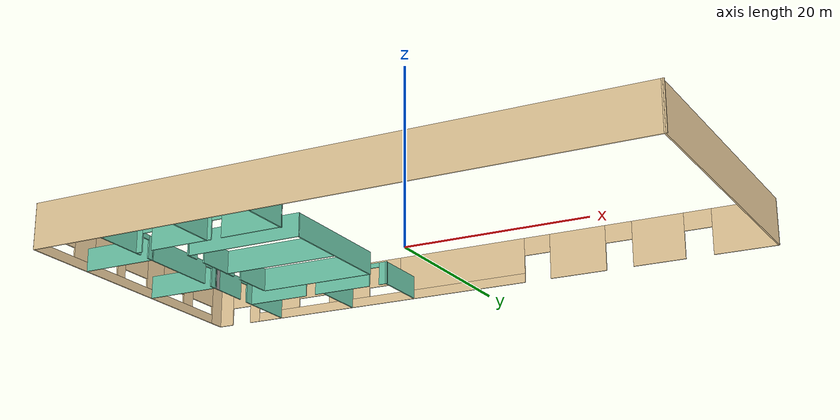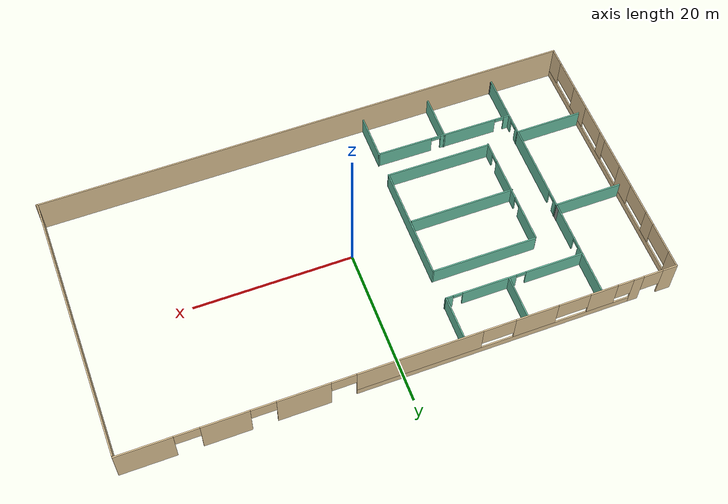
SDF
<?xml version='1.0'?>
<sdf version='1.6'>
  <model name='myWarehouse'>
    <link name='Wall_0'>
      <pose frame=''>-0.070182 16.8917 0 0 -0 0.003828</pose>
      <self_collide>0</self_collide>
      <kinematic>0</kinematic>
      <visual name='Wall_0_Visual_0'>
        <pose frame=''>-32.8034 0 2.5 0 -0 0</pose>
        <geometry>
          <box>
            <size>1.86164 0.15 5</size>
          </box>
        </geometry>
        <material>
          <script>
            <uri>file://media/materials/scripts/gazebo.material</uri>
            <name>Gazebo/Grey</name>
          </script>
          <ambient>0.921569 0.807843 0.615686 1</ambient>
          <shader type='pixel'/>
          <diffuse>0.7 0.7 0.7 1</diffuse>
          <specular>0.01 0.01 0.01 1</specular>
          <emissive>0 0 0 1</emissive>
        </material>
        <meta>
          <layer>0</layer>
        </meta>
        <transparency>0</transparency>
        <cast_shadows>1</cast_shadows>
      </visual>
      <visual name='Wall_0_Visual_1'>
        <pose frame=''>-28.8213 0 2.5 0 -0 0</pose>
        <geometry>
          <box>
            <size>1.30258 0.15 5</size>
          </box>
        </geometry>
        <material>
          <script>
            <uri>file://media/materials/scripts/gazebo.material</uri>
            <name>Gazebo/Grey</name>
          </script>
          <ambient>0.921569 0.807843 0.615686 1</ambient>
          <shader type='pixel'/>
          <diffuse>0.7 0.7 0.7 1</diffuse>
          <specular>0.01 0.01 0.01 1</specular>
          <emissive>0 0 0 1</emissive>
        </material>
        <meta>
          <layer>0</layer>
        </meta>
        <transparency>0</transparency>
        <cast_shadows>1</cast_shadows>
      </visual>
      <visual name='Wall_0_Visual_2'>
        <pose frame=''>12.0192 0 2.5 0 -0 0</pose>
        <geometry>
          <box>
            <size>6.37575 0.15 5</size>
          </box>
        </geometry>
        <material>
          <script>
            <uri>file://media/materials/scripts/gazebo.material</uri>
            <name>Gazebo/Grey</name>
          </script>
          <ambient>0.921569 0.807843 0.615686 1</ambient>
          <shader type='pixel'/>
          <diffuse>0.7 0.7 0.7 1</diffuse>
          <specular>0.01 0.01 0.01 1</specular>
          <emissive>0 0 0 1</emissive>
        </material>
        <meta>
          <layer>0</layer>
        </meta>
        <transparency>0</transparency>
        <cast_shadows>1</cast_shadows>
      </visual>
      <visual name='Wall_0_Visual_3'>
        <pose frame=''>21.0664 0 2.5 0 -0 0</pose>
        <geometry>
          <box>
            <size>5.71874 0.15 5</size>
          </box>
        </geometry>
        <material>
          <script>
            <uri>file://media/materials/scripts/gazebo.material</uri>
            <name>Gazebo/Grey</name>
          </script>
          <ambient>0.921569 0.807843 0.615686 1</ambient>
          <shader type='pixel'/>
          <diffuse>0.7 0.7 0.7 1</diffuse>
          <specular>0.01 0.01 0.01 1</specular>
          <emissive>0 0 0 1</emissive>
        </material>
        <meta>
          <layer>0</layer>
        </meta>
        <transparency>0</transparency>
        <cast_shadows>1</cast_shadows>
      </visual>
      <visual name='Wall_0_Visual_4'>
        <pose frame=''>30.33 0 2.5 0 -0 0</pose>
        <geometry>
          <box>
            <size>6.80845 0.15 5</size>
          </box>
        </geometry>
        <material>
          <script>
            <uri>file://media/materials/scripts/gazebo.material</uri>
            <name>Gazebo/Grey</name>
          </script>
          <ambient>0.921569 0.807843 0.615686 1</ambient>
          <shader type='pixel'/>
          <diffuse>0.7 0.7 0.7 1</diffuse>
          <specular>0.01 0.01 0.01 1</specular>
          <emissive>0 0 0 1</emissive>
        </material>
        <meta>
          <layer>0</layer>
        </meta>
        <transparency>0</transparency>
        <cast_shadows>1</cast_shadows>
      </visual>
      <visual name='Wall_0_Visual_5'>
        <pose frame=''>-11.1694 0 0.5 0 -0 0</pose>
        <geometry>
          <box>
            <size>34.0013 0.15 1</size>
          </box>
        </geometry>
        <material>
          <script>
            <uri>file://media/materials/scripts/gazebo.material</uri>
            <name>Gazebo/Grey</name>
          </script>
          <ambient>0.921569 0.807843 0.615686 1</ambient>
          <shader type='pixel'/>
          <diffuse>0.7 0.7 0.7 1</diffuse>
          <specular>0.01 0.01 0.01 1</specular>
          <emissive>0 0 0 1</emissive>
        </material>
        <meta>
          <layer>0</layer>
        </meta>
        <transparency>0</transparency>
        <cast_shadows>1</cast_shadows>
      </visual>
      <visual name='Wall_0_Visual_6'>
        <pose frame=''>-24.4411 0 3 0 -0 0</pose>
        <geometry>
          <box>
            <size>3.45788 0.15 4</size>
          </box>
        </geometry>
        <material>
          <script>
            <uri>file://media/materials/scripts/gazebo.material</uri>
            <name>Gazebo/Grey</name>
          </script>
          <ambient>0.921569 0.807843 0.615686 1</ambient>
          <shader type='pixel'/>
          <diffuse>0.7 0.7 0.7 1</diffuse>
          <specular>0.01 0.01 0.01 1</specular>
          <emissive>0 0 0 1</emissive>
        </material>
        <meta>
          <layer>0</layer>
        </meta>
        <transparency>0</transparency>
        <cast_shadows>1</cast_shadows>
      </visual>
      <visual name='Wall_0_Visual_7'>
        <pose frame=''>-16.0599 0 3 0 -0 0</pose>
        <geometry>
          <box>
            <size>5.30456 0.15 4</size>
          </box>
        </geometry>
        <material>
          <script>
            <uri>file://media/materials/scripts/gazebo.material</uri>
            <name>Gazebo/Grey</name>
          </script>
          <ambient>0.921569 0.807843 0.615686 1</ambient>
          <shader type='pixel'/>
          <diffuse>0.7 0.7 0.7 1</diffuse>
          <specular>0.01 0.01 0.01 1</specular>
          <emissive>0 0 0 1</emissive>
        </material>
        <meta>
          <layer>0</layer>
        </meta>
        <transparency>0</transparency>
        <cast_shadows>1</cast_shadows>
      </visual>
      <visual name='Wall_0_Visual_8'>
        <pose frame=''>-1.78814 0 3 0 -0 0</pose>
        <geometry>
          <box>
            <size>15.2389 0.15 4</size>
          </box>
        </geometry>
        <material>
          <script>
            <uri>file://media/materials/scripts/gazebo.material</uri>
            <name>Gazebo/Grey</name>
          </script>
          <ambient>0.921569 0.807843 0.615686 1</ambient>
          <shader type='pixel'/>
          <diffuse>0.7 0.7 0.7 1</diffuse>
          <specular>0.01 0.01 0.01 1</specular>
          <emissive>0 0 0 1</emissive>
        </material>
        <meta>
          <layer>0</layer>
        </meta>
        <transparency>0</transparency>
        <cast_shadows>1</cast_shadows>
      </visual>
      <visual name='Wall_0_Visual_9'>
        <pose frame=''>-30.6726 0 3.5 0 -0 0</pose>
        <geometry>
          <box>
            <size>2.4 0.15 3</size>
          </box>
        </geometry>
        <material>
          <script>
            <uri>file://media/materials/scripts/gazebo.material</uri>
            <name>Gazebo/Grey</name>
          </script>
          <ambient>0.921569 0.807843 0.615686 1</ambient>
          <shader type='pixel'/>
          <diffuse>0.7 0.7 0.7 1</diffuse>
          <specular>0.01 0.01 0.01 1</specular>
          <emissive>0 0 0 1</emissive>
        </material>
        <meta>
          <layer>0</layer>
        </meta>
        <transparency>0</transparency>
        <cast_shadows>1</cast_shadows>
      </visual>
      <visual name='Wall_0_Visual_10'>
        <pose frame=''>-27.17 0 3.5 0 -0 0</pose>
        <geometry>
          <box>
            <size>2 0.15 3</size>
          </box>
        </geometry>
        <material>
          <script>
            <uri>file://media/materials/scripts/gazebo.material</uri>
            <name>Gazebo/Grey</name>
          </script>
          <ambient>0.921569 0.807843 0.615686 1</ambient>
          <shader type='pixel'/>
          <diffuse>0.7 0.7 0.7 1</diffuse>
          <specular>0.01 0.01 0.01 1</specular>
          <emissive>0 0 0 1</emissive>
        </material>
        <meta>
          <layer>0</layer>
        </meta>
        <transparency>0</transparency>
        <cast_shadows>1</cast_shadows>
      </visual>
      <visual name='Wall_0_Visual_11'>
        <pose frame=''>-20.7121 0 3.5 0 -0 0</pose>
        <geometry>
          <box>
            <size>4 0.15 3</size>
          </box>
        </geometry>
        <material>
          <script>
            <uri>file://media/materials/scripts/gazebo.material</uri>
            <name>Gazebo/Grey</name>
          </script>
          <ambient>0.921569 0.807843 0.615686 1</ambient>
          <shader type='pixel'/>
          <diffuse>0.7 0.7 0.7 1</diffuse>
          <specular>0.01 0.01 0.01 1</specular>
          <emissive>0 0 0 1</emissive>
        </material>
        <meta>
          <layer>0</layer>
        </meta>
        <transparency>0</transparency>
        <cast_shadows>1</cast_shadows>
      </visual>
      <visual name='Wall_0_Visual_12'>
        <pose frame=''>-11.4076 0 3.5 0 -0 0</pose>
        <geometry>
          <box>
            <size>4 0.15 3</size>
          </box>
        </geometry>
        <material>
          <script>
            <uri>file://media/materials/scripts/gazebo.material</uri>
            <name>Gazebo/Grey</name>
          </script>
          <ambient>0.921569 0.807843 0.615686 1</ambient>
          <shader type='pixel'/>
          <diffuse>0.7 0.7 0.7 1</diffuse>
          <specular>0.01 0.01 0.01 1</specular>
          <emissive>0 0 0 1</emissive>
        </material>
        <meta>
          <layer>0</layer>
        </meta>
        <transparency>0</transparency>
        <cast_shadows>1</cast_shadows>
      </visual>
      <visual name='Wall_0_Visual_13'>
        <pose frame=''>16.707 0 4 0 -0 0</pose>
        <geometry>
          <box>
            <size>3 0.15 2</size>
          </box>
        </geometry>
        <material>
          <script>
            <uri>file://media/materials/scripts/gazebo.material</uri>
            <name>Gazebo/Grey</name>
          </script>
          <ambient>0.921569 0.807843 0.615686 1</ambient>
          <shader type='pixel'/>
          <diffuse>0.7 0.7 0.7 1</diffuse>
          <specular>0.01 0.01 0.01 1</specular>
          <emissive>0 0 0 1</emissive>
        </material>
        <meta>
          <layer>0</layer>
        </meta>
        <transparency>0</transparency>
        <cast_shadows>1</cast_shadows>
      </visual>
      <visual name='Wall_0_Visual_14'>
        <pose frame=''>25.4258 0 4 0 -0 0</pose>
        <geometry>
          <box>
            <size>3 0.15 2</size>
          </box>
        </geometry>
        <material>
          <script>
            <uri>file://media/materials/scripts/gazebo.material</uri>
            <name>Gazebo/Grey</name>
          </script>
          <ambient>0.921569 0.807843 0.615686 1</ambient>
          <shader type='pixel'/>
          <diffuse>0.7 0.7 0.7 1</diffuse>
          <specular>0.01 0.01 0.01 1</specular>
          <emissive>0 0 0 1</emissive>
        </material>
        <meta>
          <layer>0</layer>
        </meta>
        <transparency>0</transparency>
        <cast_shadows>1</cast_shadows>
      </visual>
      <visual name='Wall_0_Visual_15'>
        <pose frame=''>7.33129 0 4 0 -0 0</pose>
        <geometry>
          <box>
            <size>3 0.15 2</size>
          </box>
        </geometry>
        <material>
          <script>
            <uri>file://media/materials/scripts/gazebo.material</uri>
            <name>Gazebo/Grey</name>
          </script>
          <ambient>0.921569 0.807843 0.615686 1</ambient>
          <shader type='pixel'/>
          <diffuse>0.7 0.7 0.7 1</diffuse>
          <specular>0.01 0.01 0.01 1</specular>
          <emissive>0 0 0 1</emissive>
        </material>
        <meta>
          <layer>0</layer>
        </meta>
        <transparency>0</transparency>
        <cast_shadows>1</cast_shadows>
      </visual>
      <collision name='Wall_0_Collision_0'>
        <laser_retro>0</laser_retro>
        <max_contacts>10</max_contacts>
        <pose frame=''>-32.8034 0 2.5 0 -0 0</pose>
        <geometry>
          <box>
            <size>1.86164 0.15 5</size>
          </box>
        </geometry>
        <surface>
          <friction>
            <ode>
              <mu>1</mu>
              <mu2>1</mu2>
              <fdir1>0 0 0</fdir1>
              <slip1>0</slip1>
              <slip2>0</slip2>
            </ode>
            <torsional>
              <coefficient>1</coefficient>
              <patch_radius>0</patch_radius>
              <surface_radius>0</surface_radius>
              <use_patch_radius>1</use_patch_radius>
              <ode>
                <slip>0</slip>
              </ode>
            </torsional>
          </friction>
          <bounce>
            <restitution_coefficient>0</restitution_coefficient>
            <threshold>1e+06</threshold>
          </bounce>
          <contact>
            <collide_without_contact>0</collide_without_contact>
            <collide_without_contact_bitmask>1</collide_without_contact_bitmask>
            <collide_bitmask>1</collide_bitmask>
            <ode>
              <soft_cfm>0</soft_cfm>
              <soft_erp>0.2</soft_erp>
              <kp>1e+13</kp>
              <kd>1</kd>
              <max_vel>0.01</max_vel>
              <min_depth>0</min_depth>
            </ode>
            <bullet>
              <split_impulse>1</split_impulse>
              <split_impulse_penetration_threshold>-0.01</split_impulse_penetration_threshold>
              <soft_cfm>0</soft_cfm>
              <soft_erp>0.2</soft_erp>
              <kp>1e+13</kp>
              <kd>1</kd>
            </bullet>
          </contact>
        </surface>
      </collision>
      <collision name='Wall_0_Collision_1'>
        <laser_retro>0</laser_retro>
        <max_contacts>10</max_contacts>
        <pose frame=''>-28.8213 0 2.5 0 -0 0</pose>
        <geometry>
          <box>
            <size>1.30258 0.15 5</size>
          </box>
        </geometry>
        <surface>
          <friction>
            <ode>
              <mu>1</mu>
              <mu2>1</mu2>
              <fdir1>0 0 0</fdir1>
              <slip1>0</slip1>
              <slip2>0</slip2>
            </ode>
            <torsional>
              <coefficient>1</coefficient>
              <patch_radius>0</patch_radius>
              <surface_radius>0</surface_radius>
              <use_patch_radius>1</use_patch_radius>
              <ode>
                <slip>0</slip>
              </ode>
            </torsional>
          </friction>
          <bounce>
            <restitution_coefficient>0</restitution_coefficient>
            <threshold>1e+06</threshold>
          </bounce>
          <contact>
            <collide_without_contact>0</collide_without_contact>
            <collide_without_contact_bitmask>1</collide_without_contact_bitmask>
            <collide_bitmask>1</collide_bitmask>
            <ode>
              <soft_cfm>0</soft_cfm>
              <soft_erp>0.2</soft_erp>
              <kp>1e+13</kp>
              <kd>1</kd>
              <max_vel>0.01</max_vel>
              <min_depth>0</min_depth>
            </ode>
            <bullet>
              <split_impulse>1</split_impulse>
              <split_impulse_penetration_threshold>-0.01</split_impulse_penetration_threshold>
              <soft_cfm>0</soft_cfm>
              <soft_erp>0.2</soft_erp>
              <kp>1e+13</kp>
              <kd>1</kd>
            </bullet>
          </contact>
        </surface>
      </collision>
      <collision name='Wall_0_Collision_2'>
        <laser_retro>0</laser_retro>
        <max_contacts>10</max_contacts>
        <pose frame=''>12.0192 0 2.5 0 -0 0</pose>
        <geometry>
          <box>
            <size>6.37575 0.15 5</size>
          </box>
        </geometry>
        <surface>
          <friction>
            <ode>
              <mu>1</mu>
              <mu2>1</mu2>
              <fdir1>0 0 0</fdir1>
              <slip1>0</slip1>
              <slip2>0</slip2>
            </ode>
            <torsional>
              <coefficient>1</coefficient>
              <patch_radius>0</patch_radius>
              <surface_radius>0</surface_radius>
              <use_patch_radius>1</use_patch_radius>
              <ode>
                <slip>0</slip>
              </ode>
            </torsional>
          </friction>
          <bounce>
            <restitution_coefficient>0</restitution_coefficient>
            <threshold>1e+06</threshold>
          </bounce>
          <contact>
            <collide_without_contact>0</collide_without_contact>
            <collide_without_contact_bitmask>1</collide_without_contact_bitmask>
            <collide_bitmask>1</collide_bitmask>
            <ode>
              <soft_cfm>0</soft_cfm>
              <soft_erp>0.2</soft_erp>
              <kp>1e+13</kp>
              <kd>1</kd>
              <max_vel>0.01</max_vel>
              <min_depth>0</min_depth>
            </ode>
            <bullet>
              <split_impulse>1</split_impulse>
              <split_impulse_penetration_threshold>-0.01</split_impulse_penetration_threshold>
              <soft_cfm>0</soft_cfm>
              <soft_erp>0.2</soft_erp>
              <kp>1e+13</kp>
              <kd>1</kd>
            </bullet>
          </contact>
        </surface>
      </collision>
      <collision name='Wall_0_Collision_3'>
        <laser_retro>0</laser_retro>
        <max_contacts>10</max_contacts>
        <pose frame=''>21.0664 0 2.5 0 -0 0</pose>
        <geometry>
          <box>
            <size>5.71874 0.15 5</size>
          </box>
        </geometry>
        <surface>
          <friction>
            <ode>
              <mu>1</mu>
              <mu2>1</mu2>
              <fdir1>0 0 0</fdir1>
              <slip1>0</slip1>
              <slip2>0</slip2>
            </ode>
            <torsional>
              <coefficient>1</coefficient>
              <patch_radius>0</patch_radius>
              <surface_radius>0</surface_radius>
              <use_patch_radius>1</use_patch_radius>
              <ode>
                <slip>0</slip>
              </ode>
            </torsional>
          </friction>
          <bounce>
            <restitution_coefficient>0</restitution_coefficient>
            <threshold>1e+06</threshold>
          </bounce>
          <contact>
            <collide_without_contact>0</collide_without_contact>
            <collide_without_contact_bitmask>1</collide_without_contact_bitmask>
            <collide_bitmask>1</collide_bitmask>
            <ode>
              <soft_cfm>0</soft_cfm>
              <soft_erp>0.2</soft_erp>
              <kp>1e+13</kp>
              <kd>1</kd>
              <max_vel>0.01</max_vel>
              <min_depth>0</min_depth>
            </ode>
            <bullet>
              <split_impulse>1</split_impulse>
              <split_impulse_penetration_threshold>-0.01</split_impulse_penetration_threshold>
              <soft_cfm>0</soft_cfm>
              <soft_erp>0.2</soft_erp>
              <kp>1e+13</kp>
              <kd>1</kd>
            </bullet>
          </contact>
        </surface>
      </collision>
      <collision name='Wall_0_Collision_4'>
        <laser_retro>0</laser_retro>
        <max_contacts>10</max_contacts>
        <pose frame=''>30.33 0 2.5 0 -0 0</pose>
        <geometry>
          <box>
            <size>6.80845 0.15 5</size>
          </box>
        </geometry>
        <surface>
          <friction>
            <ode>
              <mu>1</mu>
              <mu2>1</mu2>
              <fdir1>0 0 0</fdir1>
              <slip1>0</slip1>
              <slip2>0</slip2>
            </ode>
            <torsional>
              <coefficient>1</coefficient>
              <patch_radius>0</patch_radius>
              <surface_radius>0</surface_radius>
              <use_patch_radius>1</use_patch_radius>
              <ode>
                <slip>0</slip>
              </ode>
            </torsional>
          </friction>
          <bounce>
            <restitution_coefficient>0</restitution_coefficient>
            <threshold>1e+06</threshold>
          </bounce>
          <contact>
            <collide_without_contact>0</collide_without_contact>
            <collide_without_contact_bitmask>1</collide_without_contact_bitmask>
            <collide_bitmask>1</collide_bitmask>
            <ode>
              <soft_cfm>0</soft_cfm>
              <soft_erp>0.2</soft_erp>
              <kp>1e+13</kp>
              <kd>1</kd>
              <max_vel>0.01</max_vel>
              <min_depth>0</min_depth>
            </ode>
            <bullet>
              <split_impulse>1</split_impulse>
              <split_impulse_penetration_threshold>-0.01</split_impulse_penetration_threshold>
              <soft_cfm>0</soft_cfm>
              <soft_erp>0.2</soft_erp>
              <kp>1e+13</kp>
              <kd>1</kd>
            </bullet>
          </contact>
        </surface>
      </collision>
      <collision name='Wall_0_Collision_5'>
        <laser_retro>0</laser_retro>
        <max_contacts>10</max_contacts>
        <pose frame=''>-11.1694 0 0.5 0 -0 0</pose>
        <geometry>
          <box>
            <size>34.0013 0.15 1</size>
          </box>
        </geometry>
        <surface>
          <friction>
            <ode>
              <mu>1</mu>
              <mu2>1</mu2>
              <fdir1>0 0 0</fdir1>
              <slip1>0</slip1>
              <slip2>0</slip2>
            </ode>
            <torsional>
              <coefficient>1</coefficient>
              <patch_radius>0</patch_radius>
              <surface_radius>0</surface_radius>
              <use_patch_radius>1</use_patch_radius>
              <ode>
                <slip>0</slip>
              </ode>
            </torsional>
          </friction>
          <bounce>
            <restitution_coefficient>0</restitution_coefficient>
            <threshold>1e+06</threshold>
          </bounce>
          <contact>
            <collide_without_contact>0</collide_without_contact>
            <collide_without_contact_bitmask>1</collide_without_contact_bitmask>
            <collide_bitmask>1</collide_bitmask>
            <ode>
              <soft_cfm>0</soft_cfm>
              <soft_erp>0.2</soft_erp>
              <kp>1e+13</kp>
              <kd>1</kd>
              <max_vel>0.01</max_vel>
              <min_depth>0</min_depth>
            </ode>
            <bullet>
              <split_impulse>1</split_impulse>
              <split_impulse_penetration_threshold>-0.01</split_impulse_penetration_threshold>
              <soft_cfm>0</soft_cfm>
              <soft_erp>0.2</soft_erp>
              <kp>1e+13</kp>
              <kd>1</kd>
            </bullet>
          </contact>
        </surface>
      </collision>
      <collision name='Wall_0_Collision_7'>
        <laser_retro>0</laser_retro>
        <max_contacts>10</max_contacts>
        <pose frame=''>-16.0599 0 3 0 -0 0</pose>
        <geometry>
          <box>
            <size>5.30456 0.15 4</size>
          </box>
        </geometry>
        <surface>
          <friction>
            <ode>
              <mu>1</mu>
              <mu2>1</mu2>
              <fdir1>0 0 0</fdir1>
              <slip1>0</slip1>
              <slip2>0</slip2>
            </ode>
            <torsional>
              <coefficient>1</coefficient>
              <patch_radius>0</patch_radius>
              <surface_radius>0</surface_radius>
              <use_patch_radius>1</use_patch_radius>
              <ode>
                <slip>0</slip>
              </ode>
            </torsional>
          </friction>
          <bounce>
            <restitution_coefficient>0</restitution_coefficient>
            <threshold>1e+06</threshold>
          </bounce>
          <contact>
            <collide_without_contact>0</collide_without_contact>
            <collide_without_contact_bitmask>1</collide_without_contact_bitmask>
            <collide_bitmask>1</collide_bitmask>
            <ode>
              <soft_cfm>0</soft_cfm>
              <soft_erp>0.2</soft_erp>
              <kp>1e+13</kp>
              <kd>1</kd>
              <max_vel>0.01</max_vel>
              <min_depth>0</min_depth>
            </ode>
            <bullet>
              <split_impulse>1</split_impulse>
              <split_impulse_penetration_threshold>-0.01</split_impulse_penetration_threshold>
              <soft_cfm>0</soft_cfm>
              <soft_erp>0.2</soft_erp>
              <kp>1e+13</kp>
              <kd>1</kd>
            </bullet>
          </contact>
        </surface>
      </collision>
      <collision name='Wall_0_Collision_6'>
        <laser_retro>0</laser_retro>
        <max_contacts>10</max_contacts>
        <pose frame=''>-24.4411 0 3 0 -0 0</pose>
        <geometry>
          <box>
            <size>3.45788 0.15 4</size>
          </box>
        </geometry>
        <surface>
          <friction>
            <ode>
              <mu>1</mu>
              <mu2>1</mu2>
              <fdir1>0 0 0</fdir1>
              <slip1>0</slip1>
              <slip2>0</slip2>
            </ode>
            <torsional>
              <coefficient>1</coefficient>
              <patch_radius>0</patch_radius>
              <surface_radius>0</surface_radius>
              <use_patch_radius>1</use_patch_radius>
              <ode>
                <slip>0</slip>
              </ode>
            </torsional>
          </friction>
          <bounce>
            <restitution_coefficient>0</restitution_coefficient>
            <threshold>1e+06</threshold>
          </bounce>
          <contact>
            <collide_without_contact>0</collide_without_contact>
            <collide_without_contact_bitmask>1</collide_without_contact_bitmask>
            <collide_bitmask>1</collide_bitmask>
            <ode>
              <soft_cfm>0</soft_cfm>
              <soft_erp>0.2</soft_erp>
              <kp>1e+13</kp>
              <kd>1</kd>
              <max_vel>0.01</max_vel>
              <min_depth>0</min_depth>
            </ode>
            <bullet>
              <split_impulse>1</split_impulse>
              <split_impulse_penetration_threshold>-0.01</split_impulse_penetration_threshold>
              <soft_cfm>0</soft_cfm>
              <soft_erp>0.2</soft_erp>
              <kp>1e+13</kp>
              <kd>1</kd>
            </bullet>
          </contact>
        </surface>
      </collision>
      <collision name='Wall_0_Collision_10'>
        <laser_retro>0</laser_retro>
        <max_contacts>10</max_contacts>
        <pose frame=''>-27.17 0 3.5 0 -0 0</pose>
        <geometry>
          <box>
            <size>2 0.15 3</size>
          </box>
        </geometry>
        <surface>
          <friction>
            <ode>
              <mu>1</mu>
              <mu2>1</mu2>
              <fdir1>0 0 0</fdir1>
              <slip1>0</slip1>
              <slip2>0</slip2>
            </ode>
            <torsional>
              <coefficient>1</coefficient>
              <patch_radius>0</patch_radius>
              <surface_radius>0</surface_radius>
              <use_patch_radius>1</use_patch_radius>
              <ode>
                <slip>0</slip>
              </ode>
            </torsional>
          </friction>
          <bounce>
            <restitution_coefficient>0</restitution_coefficient>
            <threshold>1e+06</threshold>
          </bounce>
          <contact>
            <collide_without_contact>0</collide_without_contact>
            <collide_without_contact_bitmask>1</collide_without_contact_bitmask>
            <collide_bitmask>1</collide_bitmask>
            <ode>
              <soft_cfm>0</soft_cfm>
              <soft_erp>0.2</soft_erp>
              <kp>1e+13</kp>
              <kd>1</kd>
              <max_vel>0.01</max_vel>
              <min_depth>0</min_depth>
            </ode>
            <bullet>
              <split_impulse>1</split_impulse>
              <split_impulse_penetration_threshold>-0.01</split_impulse_penetration_threshold>
              <soft_cfm>0</soft_cfm>
              <soft_erp>0.2</soft_erp>
              <kp>1e+13</kp>
              <kd>1</kd>
            </bullet>
          </contact>
        </surface>
      </collision>
      <collision name='Wall_0_Collision_8'>
        <laser_retro>0</laser_retro>
        <max_contacts>10</max_contacts>
        <pose frame=''>-1.78814 0 3 0 -0 0</pose>
        <geometry>
          <box>
            <size>15.2389 0.15 4</size>
          </box>
        </geometry>
        <surface>
          <friction>
            <ode>
              <mu>1</mu>
              <mu2>1</mu2>
              <fdir1>0 0 0</fdir1>
              <slip1>0</slip1>
              <slip2>0</slip2>
            </ode>
            <torsional>
              <coefficient>1</coefficient>
              <patch_radius>0</patch_radius>
              <surface_radius>0</surface_radius>
              <use_patch_radius>1</use_patch_radius>
              <ode>
                <slip>0</slip>
              </ode>
            </torsional>
          </friction>
          <bounce>
            <restitution_coefficient>0</restitution_coefficient>
            <threshold>1e+06</threshold>
          </bounce>
          <contact>
            <collide_without_contact>0</collide_without_contact>
            <collide_without_contact_bitmask>1</collide_without_contact_bitmask>
            <collide_bitmask>1</collide_bitmask>
            <ode>
              <soft_cfm>0</soft_cfm>
              <soft_erp>0.2</soft_erp>
              <kp>1e+13</kp>
              <kd>1</kd>
              <max_vel>0.01</max_vel>
              <min_depth>0</min_depth>
            </ode>
            <bullet>
              <split_impulse>1</split_impulse>
              <split_impulse_penetration_threshold>-0.01</split_impulse_penetration_threshold>
              <soft_cfm>0</soft_cfm>
              <soft_erp>0.2</soft_erp>
              <kp>1e+13</kp>
              <kd>1</kd>
            </bullet>
          </contact>
        </surface>
      </collision>
      <collision name='Wall_0_Collision_9'>
        <laser_retro>0</laser_retro>
        <max_contacts>10</max_contacts>
        <pose frame=''>-30.6726 0 3.5 0 -0 0</pose>
        <geometry>
          <box>
            <size>2.4 0.15 3</size>
          </box>
        </geometry>
        <surface>
          <friction>
            <ode>
              <mu>1</mu>
              <mu2>1</mu2>
              <fdir1>0 0 0</fdir1>
              <slip1>0</slip1>
              <slip2>0</slip2>
            </ode>
            <torsional>
              <coefficient>1</coefficient>
              <patch_radius>0</patch_radius>
              <surface_radius>0</surface_radius>
              <use_patch_radius>1</use_patch_radius>
              <ode>
                <slip>0</slip>
              </ode>
            </torsional>
          </friction>
          <bounce>
            <restitution_coefficient>0</restitution_coefficient>
            <threshold>1e+06</threshold>
          </bounce>
          <contact>
            <collide_without_contact>0</collide_without_contact>
            <collide_without_contact_bitmask>1</collide_without_contact_bitmask>
            <collide_bitmask>1</collide_bitmask>
            <ode>
              <soft_cfm>0</soft_cfm>
              <soft_erp>0.2</soft_erp>
              <kp>1e+13</kp>
              <kd>1</kd>
              <max_vel>0.01</max_vel>
              <min_depth>0</min_depth>
            </ode>
            <bullet>
              <split_impulse>1</split_impulse>
              <split_impulse_penetration_threshold>-0.01</split_impulse_penetration_threshold>
              <soft_cfm>0</soft_cfm>
              <soft_erp>0.2</soft_erp>
              <kp>1e+13</kp>
              <kd>1</kd>
            </bullet>
          </contact>
        </surface>
      </collision>
      <collision name='Wall_0_Collision_11'>
        <laser_retro>0</laser_retro>
        <max_contacts>10</max_contacts>
        <pose frame=''>-20.7121 0 3.5 0 -0 0</pose>
        <geometry>
          <box>
            <size>4 0.15 3</size>
          </box>
        </geometry>
        <surface>
          <friction>
            <ode>
              <mu>1</mu>
              <mu2>1</mu2>
              <fdir1>0 0 0</fdir1>
              <slip1>0</slip1>
              <slip2>0</slip2>
            </ode>
            <torsional>
              <coefficient>1</coefficient>
              <patch_radius>0</patch_radius>
              <surface_radius>0</surface_radius>
              <use_patch_radius>1</use_patch_radius>
              <ode>
                <slip>0</slip>
              </ode>
            </torsional>
          </friction>
          <bounce>
            <restitution_coefficient>0</restitution_coefficient>
            <threshold>1e+06</threshold>
          </bounce>
          <contact>
            <collide_without_contact>0</collide_without_contact>
            <collide_without_contact_bitmask>1</collide_without_contact_bitmask>
            <collide_bitmask>1</collide_bitmask>
            <ode>
              <soft_cfm>0</soft_cfm>
              <soft_erp>0.2</soft_erp>
              <kp>1e+13</kp>
              <kd>1</kd>
              <max_vel>0.01</max_vel>
              <min_depth>0</min_depth>
            </ode>
            <bullet>
              <split_impulse>1</split_impulse>
              <split_impulse_penetration_threshold>-0.01</split_impulse_penetration_threshold>
              <soft_cfm>0</soft_cfm>
              <soft_erp>0.2</soft_erp>
              <kp>1e+13</kp>
              <kd>1</kd>
            </bullet>
          </contact>
        </surface>
      </collision>
      <collision name='Wall_0_Collision_12'>
        <laser_retro>0</laser_retro>
        <max_contacts>10</max_contacts>
        <pose frame=''>-11.4076 0 3.5 0 -0 0</pose>
        <geometry>
          <box>
            <size>4 0.15 3</size>
          </box>
        </geometry>
        <surface>
          <friction>
            <ode>
              <mu>1</mu>
              <mu2>1</mu2>
              <fdir1>0 0 0</fdir1>
              <slip1>0</slip1>
              <slip2>0</slip2>
            </ode>
            <torsional>
              <coefficient>1</coefficient>
              <patch_radius>0</patch_radius>
              <surface_radius>0</surface_radius>
              <use_patch_radius>1</use_patch_radius>
              <ode>
                <slip>0</slip>
              </ode>
            </torsional>
          </friction>
          <bounce>
            <restitution_coefficient>0</restitution_coefficient>
            <threshold>1e+06</threshold>
          </bounce>
          <contact>
            <collide_without_contact>0</collide_without_contact>
            <collide_without_contact_bitmask>1</collide_without_contact_bitmask>
            <collide_bitmask>1</collide_bitmask>
            <ode>
              <soft_cfm>0</soft_cfm>
              <soft_erp>0.2</soft_erp>
              <kp>1e+13</kp>
              <kd>1</kd>
              <max_vel>0.01</max_vel>
              <min_depth>0</min_depth>
            </ode>
            <bullet>
              <split_impulse>1</split_impulse>
              <split_impulse_penetration_threshold>-0.01</split_impulse_penetration_threshold>
              <soft_cfm>0</soft_cfm>
              <soft_erp>0.2</soft_erp>
              <kp>1e+13</kp>
              <kd>1</kd>
            </bullet>
          </contact>
        </surface>
      </collision>
      <collision name='Wall_0_Collision_13'>
        <laser_retro>0</laser_retro>
        <max_contacts>10</max_contacts>
        <pose frame=''>16.707 0 4 0 -0 0</pose>
        <geometry>
          <box>
            <size>3 0.15 2</size>
          </box>
        </geometry>
        <surface>
          <friction>
            <ode>
              <mu>1</mu>
              <mu2>1</mu2>
              <fdir1>0 0 0</fdir1>
              <slip1>0</slip1>
              <slip2>0</slip2>
            </ode>
            <torsional>
              <coefficient>1</coefficient>
              <patch_radius>0</patch_radius>
              <surface_radius>0</surface_radius>
              <use_patch_radius>1</use_patch_radius>
              <ode>
                <slip>0</slip>
              </ode>
            </torsional>
          </friction>
          <bounce>
            <restitution_coefficient>0</restitution_coefficient>
            <threshold>1e+06</threshold>
          </bounce>
          <contact>
            <collide_without_contact>0</collide_without_contact>
            <collide_without_contact_bitmask>1</collide_without_contact_bitmask>
            <collide_bitmask>1</collide_bitmask>
            <ode>
              <soft_cfm>0</soft_cfm>
              <soft_erp>0.2</soft_erp>
              <kp>1e+13</kp>
              <kd>1</kd>
              <max_vel>0.01</max_vel>
              <min_depth>0</min_depth>
            </ode>
            <bullet>
              <split_impulse>1</split_impulse>
              <split_impulse_penetration_threshold>-0.01</split_impulse_penetration_threshold>
              <soft_cfm>0</soft_cfm>
              <soft_erp>0.2</soft_erp>
              <kp>1e+13</kp>
              <kd>1</kd>
            </bullet>
          </contact>
        </surface>
      </collision>
      <collision name='Wall_0_Collision_14'>
        <laser_retro>0</laser_retro>
        <max_contacts>10</max_contacts>
        <pose frame=''>25.4258 0 4 0 -0 0</pose>
        <geometry>
          <box>
            <size>3 0.15 2</size>
          </box>
        </geometry>
        <surface>
          <friction>
            <ode>
              <mu>1</mu>
              <mu2>1</mu2>
              <fdir1>0 0 0</fdir1>
              <slip1>0</slip1>
              <slip2>0</slip2>
            </ode>
            <torsional>
              <coefficient>1</coefficient>
              <patch_radius>0</patch_radius>
              <surface_radius>0</surface_radius>
              <use_patch_radius>1</use_patch_radius>
              <ode>
                <slip>0</slip>
              </ode>
            </torsional>
          </friction>
          <bounce>
            <restitution_coefficient>0</restitution_coefficient>
            <threshold>1e+06</threshold>
          </bounce>
          <contact>
            <collide_without_contact>0</collide_without_contact>
            <collide_without_contact_bitmask>1</collide_without_contact_bitmask>
            <collide_bitmask>1</collide_bitmask>
            <ode>
              <soft_cfm>0</soft_cfm>
              <soft_erp>0.2</soft_erp>
              <kp>1e+13</kp>
              <kd>1</kd>
              <max_vel>0.01</max_vel>
              <min_depth>0</min_depth>
            </ode>
            <bullet>
              <split_impulse>1</split_impulse>
              <split_impulse_penetration_threshold>-0.01</split_impulse_penetration_threshold>
              <soft_cfm>0</soft_cfm>
              <soft_erp>0.2</soft_erp>
              <kp>1e+13</kp>
              <kd>1</kd>
            </bullet>
          </contact>
        </surface>
      </collision>
      <collision name='Wall_0_Collision_15'>
        <laser_retro>0</laser_retro>
        <max_contacts>10</max_contacts>
        <pose frame=''>7.33129 0 4 0 -0 0</pose>
        <geometry>
          <box>
            <size>3 0.15 2</size>
          </box>
        </geometry>
        <surface>
          <friction>
            <ode>
              <mu>1</mu>
              <mu2>1</mu2>
              <fdir1>0 0 0</fdir1>
              <slip1>0</slip1>
              <slip2>0</slip2>
            </ode>
            <torsional>
              <coefficient>1</coefficient>
              <patch_radius>0</patch_radius>
              <surface_radius>0</surface_radius>
              <use_patch_radius>1</use_patch_radius>
              <ode>
                <slip>0</slip>
              </ode>
            </torsional>
          </friction>
          <bounce>
            <restitution_coefficient>0</restitution_coefficient>
            <threshold>1e+06</threshold>
          </bounce>
          <contact>
            <collide_without_contact>0</collide_without_contact>
            <collide_without_contact_bitmask>1</collide_without_contact_bitmask>
            <collide_bitmask>1</collide_bitmask>
            <ode>
              <soft_cfm>0</soft_cfm>
              <soft_erp>0.2</soft_erp>
              <kp>1e+13</kp>
              <kd>1</kd>
              <max_vel>0.01</max_vel>
              <min_depth>0</min_depth>
            </ode>
            <bullet>
              <split_impulse>1</split_impulse>
              <split_impulse_penetration_threshold>-0.01</split_impulse_penetration_threshold>
              <soft_cfm>0</soft_cfm>
              <soft_erp>0.2</soft_erp>
              <kp>1e+13</kp>
              <kd>1</kd>
            </bullet>
          </contact>
        </surface>
      </collision>
    </link>
    <link name='Wall_1'>
      <pose frame=''>33.5887 -0.095862 0 0 0 -1.5708</pose>
      <self_collide>0</self_collide>
      <kinematic>0</kinematic>
      <visual name='Wall_1_Visual'>
        <pose frame=''>0 0 2.5 0 -0 0</pose>
        <geometry>
          <box>
            <size>34 0.15 5</size>
          </box>
        </geometry>
        <material>
          <script>
            <uri>file://media/materials/scripts/gazebo.material</uri>
            <name>Gazebo/Grey</name>
          </script>
          <ambient>0.921569 0.807843 0.615686 1</ambient>
          <shader type='pixel'/>
          <diffuse>0.7 0.7 0.7 1</diffuse>
          <specular>0.01 0.01 0.01 1</specular>
          <emissive>0 0 0 1</emissive>
        </material>
        <meta>
          <layer>0</layer>
        </meta>
        <transparency>0</transparency>
        <cast_shadows>1</cast_shadows>
      </visual>
      <collision name='Wall_1_Collision'>
        <laser_retro>0</laser_retro>
        <max_contacts>10</max_contacts>
        <pose frame=''>0 0 2.5 0 -0 0</pose>
        <geometry>
          <box>
            <size>34 0.15 5</size>
          </box>
        </geometry>
        <surface>
          <friction>
            <ode>
              <mu>1</mu>
              <mu2>1</mu2>
              <fdir1>0 0 0</fdir1>
              <slip1>0</slip1>
              <slip2>0</slip2>
            </ode>
            <torsional>
              <coefficient>1</coefficient>
              <patch_radius>0</patch_radius>
              <surface_radius>0</surface_radius>
              <use_patch_radius>1</use_patch_radius>
              <ode>
                <slip>0</slip>
              </ode>
            </torsional>
          </friction>
          <bounce>
            <restitution_coefficient>0</restitution_coefficient>
            <threshold>1e+06</threshold>
          </bounce>
          <contact>
            <collide_without_contact>0</collide_without_contact>
            <collide_without_contact_bitmask>1</collide_without_contact_bitmask>
            <collide_bitmask>1</collide_bitmask>
            <ode>
              <soft_cfm>0</soft_cfm>
              <soft_erp>0.2</soft_erp>
              <kp>1e+13</kp>
              <kd>1</kd>
              <max_vel>0.01</max_vel>
              <min_depth>0</min_depth>
            </ode>
            <bullet>
              <split_impulse>1</split_impulse>
              <split_impulse_penetration_threshold>-0.01</split_impulse_penetration_threshold>
              <soft_cfm>0</soft_cfm>
              <soft_erp>0.2</soft_erp>
              <kp>1e+13</kp>
              <kd>1</kd>
            </bullet>
          </contact>
        </surface>
      </collision>
    </link>
    <link name='Wall_12'>
      <pose frame=''>-16.3895 10.2886 0 0 -0 0</pose>
      <self_collide>0</self_collide>
      <kinematic>0</kinematic>
      <visual name='Wall_12_Visual_0'>
        <pose frame=''>-5.13222 0 1.25 0 -0 0</pose>
        <geometry>
          <box>
            <size>7.23555 0.15 2.5</size>
          </box>
        </geometry>
        <material>
          <script>
            <uri>file://media/materials/scripts/gazebo.material</uri>
            <name>Gazebo/Grey</name>
          </script>
          <ambient>0.435294 0.796078 0.67451 1</ambient>
          <shader type='pixel'/>
          <diffuse>0.7 0.7 0.7 1</diffuse>
          <specular>0.01 0.01 0.01 1</specular>
          <emissive>0 0 0 1</emissive>
        </material>
        <meta>
          <layer>0</layer>
        </meta>
        <transparency>0</transparency>
        <cast_shadows>1</cast_shadows>
      </visual>
      <visual name='Wall_12_Visual_1'>
        <pose frame=''>3.10908 0 1.25 0 -0 0</pose>
        <geometry>
          <box>
            <size>6.84705 0.15 2.5</size>
          </box>
        </geometry>
        <material>
          <script>
            <uri>file://media/materials/scripts/gazebo.material</uri>
            <name>Gazebo/Grey</name>
          </script>
          <ambient>0.435294 0.796078 0.67451 1</ambient>
          <shader type='pixel'/>
          <diffuse>0.7 0.7 0.7 1</diffuse>
          <specular>0.01 0.01 0.01 1</specular>
          <emissive>0 0 0 1</emissive>
        </material>
        <meta>
          <layer>0</layer>
        </meta>
        <transparency>0</transparency>
        <cast_shadows>1</cast_shadows>
      </visual>
      <visual name='Wall_12_Visual_2'>
        <pose frame=''>8.2413 0 1.25 0 -0 0</pose>
        <geometry>
          <box>
            <size>1.01739 0.15 2.5</size>
          </box>
        </geometry>
        <material>
          <script>
            <uri>file://media/materials/scripts/gazebo.material</uri>
            <name>Gazebo/Grey</name>
          </script>
          <ambient>0.435294 0.796078 0.67451 1</ambient>
          <shader type='pixel'/>
          <diffuse>0.7 0.7 0.7 1</diffuse>
          <specular>0.01 0.01 0.01 1</specular>
          <emissive>0 0 0 1</emissive>
        </material>
        <meta>
          <layer>0</layer>
        </meta>
        <transparency>0</transparency>
        <cast_shadows>1</cast_shadows>
      </visual>
      <visual name='Wall_12_Visual_3'>
        <pose frame=''>-0.914447 0 2.25 0 -0 0</pose>
        <geometry>
          <box>
            <size>1.2 0.15 0.5</size>
          </box>
        </geometry>
        <material>
          <script>
            <uri>file://media/materials/scripts/gazebo.material</uri>
            <name>Gazebo/Grey</name>
          </script>
          <ambient>0.435294 0.796078 0.67451 1</ambient>
          <shader type='pixel'/>
          <diffuse>0.7 0.7 0.7 1</diffuse>
          <specular>0.01 0.01 0.01 1</specular>
          <emissive>0 0 0 1</emissive>
        </material>
        <meta>
          <layer>0</layer>
        </meta>
        <transparency>0</transparency>
        <cast_shadows>1</cast_shadows>
      </visual>
      <visual name='Wall_12_Visual_4'>
        <pose frame=''>7.13261 0 2.25 0 -0 0</pose>
        <geometry>
          <box>
            <size>1.2 0.15 0.5</size>
          </box>
        </geometry>
        <material>
          <script>
            <uri>file://media/materials/scripts/gazebo.material</uri>
            <name>Gazebo/Grey</name>
          </script>
          <ambient>0.435294 0.796078 0.67451 1</ambient>
          <shader type='pixel'/>
          <diffuse>0.7 0.7 0.7 1</diffuse>
          <specular>0.01 0.01 0.01 1</specular>
          <emissive>0 0 0 1</emissive>
        </material>
        <meta>
          <layer>0</layer>
        </meta>
        <transparency>0</transparency>
        <cast_shadows>1</cast_shadows>
      </visual>
      <collision name='Wall_12_Collision_0'>
        <laser_retro>0</laser_retro>
        <max_contacts>10</max_contacts>
        <pose frame=''>-5.13222 0 1.25 0 -0 0</pose>
        <geometry>
          <box>
            <size>7.23555 0.15 2.5</size>
          </box>
        </geometry>
        <surface>
          <friction>
            <ode>
              <mu>1</mu>
              <mu2>1</mu2>
              <fdir1>0 0 0</fdir1>
              <slip1>0</slip1>
              <slip2>0</slip2>
            </ode>
            <torsional>
              <coefficient>1</coefficient>
              <patch_radius>0</patch_radius>
              <surface_radius>0</surface_radius>
              <use_patch_radius>1</use_patch_radius>
              <ode>
                <slip>0</slip>
              </ode>
            </torsional>
          </friction>
          <bounce>
            <restitution_coefficient>0</restitution_coefficient>
            <threshold>1e+06</threshold>
          </bounce>
          <contact>
            <collide_without_contact>0</collide_without_contact>
            <collide_without_contact_bitmask>1</collide_without_contact_bitmask>
            <collide_bitmask>1</collide_bitmask>
            <ode>
              <soft_cfm>0</soft_cfm>
              <soft_erp>0.2</soft_erp>
              <kp>1e+13</kp>
              <kd>1</kd>
              <max_vel>0.01</max_vel>
              <min_depth>0</min_depth>
            </ode>
            <bullet>
              <split_impulse>1</split_impulse>
              <split_impulse_penetration_threshold>-0.01</split_impulse_penetration_threshold>
              <soft_cfm>0</soft_cfm>
              <soft_erp>0.2</soft_erp>
              <kp>1e+13</kp>
              <kd>1</kd>
            </bullet>
          </contact>
        </surface>
      </collision>
      <collision name='Wall_12_Collision_3'>
        <laser_retro>0</laser_retro>
        <max_contacts>10</max_contacts>
        <pose frame=''>-0.914447 0 2.25 0 -0 0</pose>
        <geometry>
          <box>
            <size>1.2 0.15 0.5</size>
          </box>
        </geometry>
        <surface>
          <friction>
            <ode>
              <mu>1</mu>
              <mu2>1</mu2>
              <fdir1>0 0 0</fdir1>
              <slip1>0</slip1>
              <slip2>0</slip2>
            </ode>
            <torsional>
              <coefficient>1</coefficient>
              <patch_radius>0</patch_radius>
              <surface_radius>0</surface_radius>
              <use_patch_radius>1</use_patch_radius>
              <ode>
                <slip>0</slip>
              </ode>
            </torsional>
          </friction>
          <bounce>
            <restitution_coefficient>0</restitution_coefficient>
            <threshold>1e+06</threshold>
          </bounce>
          <contact>
            <collide_without_contact>0</collide_without_contact>
            <collide_without_contact_bitmask>1</collide_without_contact_bitmask>
            <collide_bitmask>1</collide_bitmask>
            <ode>
              <soft_cfm>0</soft_cfm>
              <soft_erp>0.2</soft_erp>
              <kp>1e+13</kp>
              <kd>1</kd>
              <max_vel>0.01</max_vel>
              <min_depth>0</min_depth>
            </ode>
            <bullet>
              <split_impulse>1</split_impulse>
              <split_impulse_penetration_threshold>-0.01</split_impulse_penetration_threshold>
              <soft_cfm>0</soft_cfm>
              <soft_erp>0.2</soft_erp>
              <kp>1e+13</kp>
              <kd>1</kd>
            </bullet>
          </contact>
        </surface>
      </collision>
      <collision name='Wall_12_Collision_1'>
        <laser_retro>0</laser_retro>
        <max_contacts>10</max_contacts>
        <pose frame=''>3.10908 0 1.25 0 -0 0</pose>
        <geometry>
          <box>
            <size>6.84705 0.15 2.5</size>
          </box>
        </geometry>
        <surface>
          <friction>
            <ode>
              <mu>1</mu>
              <mu2>1</mu2>
              <fdir1>0 0 0</fdir1>
              <slip1>0</slip1>
              <slip2>0</slip2>
            </ode>
            <torsional>
              <coefficient>1</coefficient>
              <patch_radius>0</patch_radius>
              <surface_radius>0</surface_radius>
              <use_patch_radius>1</use_patch_radius>
              <ode>
                <slip>0</slip>
              </ode>
            </torsional>
          </friction>
          <bounce>
            <restitution_coefficient>0</restitution_coefficient>
            <threshold>1e+06</threshold>
          </bounce>
          <contact>
            <collide_without_contact>0</collide_without_contact>
            <collide_without_contact_bitmask>1</collide_without_contact_bitmask>
            <collide_bitmask>1</collide_bitmask>
            <ode>
              <soft_cfm>0</soft_cfm>
              <soft_erp>0.2</soft_erp>
              <kp>1e+13</kp>
              <kd>1</kd>
              <max_vel>0.01</max_vel>
              <min_depth>0</min_depth>
            </ode>
            <bullet>
              <split_impulse>1</split_impulse>
              <split_impulse_penetration_threshold>-0.01</split_impulse_penetration_threshold>
              <soft_cfm>0</soft_cfm>
              <soft_erp>0.2</soft_erp>
              <kp>1e+13</kp>
              <kd>1</kd>
            </bullet>
          </contact>
        </surface>
      </collision>
      <collision name='Wall_12_Collision_2'>
        <laser_retro>0</laser_retro>
        <max_contacts>10</max_contacts>
        <pose frame=''>8.2413 0 1.25 0 -0 0</pose>
        <geometry>
          <box>
            <size>1.01739 0.15 2.5</size>
          </box>
        </geometry>
        <surface>
          <friction>
            <ode>
              <mu>1</mu>
              <mu2>1</mu2>
              <fdir1>0 0 0</fdir1>
              <slip1>0</slip1>
              <slip2>0</slip2>
            </ode>
            <torsional>
              <coefficient>1</coefficient>
              <patch_radius>0</patch_radius>
              <surface_radius>0</surface_radius>
              <use_patch_radius>1</use_patch_radius>
              <ode>
                <slip>0</slip>
              </ode>
            </torsional>
          </friction>
          <bounce>
            <restitution_coefficient>0</restitution_coefficient>
            <threshold>1e+06</threshold>
          </bounce>
          <contact>
            <collide_without_contact>0</collide_without_contact>
            <collide_without_contact_bitmask>1</collide_without_contact_bitmask>
            <collide_bitmask>1</collide_bitmask>
            <ode>
              <soft_cfm>0</soft_cfm>
              <soft_erp>0.2</soft_erp>
              <kp>1e+13</kp>
              <kd>1</kd>
              <max_vel>0.01</max_vel>
              <min_depth>0</min_depth>
            </ode>
            <bullet>
              <split_impulse>1</split_impulse>
              <split_impulse_penetration_threshold>-0.01</split_impulse_penetration_threshold>
              <soft_cfm>0</soft_cfm>
              <soft_erp>0.2</soft_erp>
              <kp>1e+13</kp>
              <kd>1</kd>
            </bullet>
          </contact>
        </surface>
      </collision>
      <collision name='Wall_12_Collision_4'>
        <laser_retro>0</laser_retro>
        <max_contacts>10</max_contacts>
        <pose frame=''>7.13261 0 2.25 0 -0 0</pose>
        <geometry>
          <box>
            <size>1.2 0.15 0.5</size>
          </box>
        </geometry>
        <surface>
          <friction>
            <ode>
              <mu>1</mu>
              <mu2>1</mu2>
              <fdir1>0 0 0</fdir1>
              <slip1>0</slip1>
              <slip2>0</slip2>
            </ode>
            <torsional>
              <coefficient>1</coefficient>
              <patch_radius>0</patch_radius>
              <surface_radius>0</surface_radius>
              <use_patch_radius>1</use_patch_radius>
              <ode>
                <slip>0</slip>
              </ode>
            </torsional>
          </friction>
          <bounce>
            <restitution_coefficient>0</restitution_coefficient>
            <threshold>1e+06</threshold>
          </bounce>
          <contact>
            <collide_without_contact>0</collide_without_contact>
            <collide_without_contact_bitmask>1</collide_without_contact_bitmask>
            <collide_bitmask>1</collide_bitmask>
            <ode>
              <soft_cfm>0</soft_cfm>
              <soft_erp>0.2</soft_erp>
              <kp>1e+13</kp>
              <kd>1</kd>
              <max_vel>0.01</max_vel>
              <min_depth>0</min_depth>
            </ode>
            <bullet>
              <split_impulse>1</split_impulse>
              <split_impulse_penetration_threshold>-0.01</split_impulse_penetration_threshold>
              <soft_cfm>0</soft_cfm>
              <soft_erp>0.2</soft_erp>
              <kp>1e+13</kp>
              <kd>1</kd>
            </bullet>
          </contact>
        </surface>
      </collision>
    </link>
    <link name='Wall_22'>
      <pose frame=''>-15.7265 13.516 0 0 -0 1.5708</pose>
      <self_collide>0</self_collide>
      <kinematic>0</kinematic>
      <visual name='Wall_22_Visual'>
        <pose frame=''>0 0 1.25 0 -0 0</pose>
        <geometry>
          <box>
            <size>6.5 0.15 2.5</size>
          </box>
        </geometry>
        <material>
          <script>
            <uri>file://media/materials/scripts/gazebo.material</uri>
            <name>Gazebo/Grey</name>
          </script>
          <ambient>0.435294 0.796078 0.67451 1</ambient>
          <shader type='pixel'/>
          <diffuse>0.7 0.7 0.7 1</diffuse>
          <specular>0.01 0.01 0.01 1</specular>
          <emissive>0 0 0 1</emissive>
        </material>
        <meta>
          <layer>0</layer>
        </meta>
        <transparency>0</transparency>
        <cast_shadows>1</cast_shadows>
      </visual>
      <collision name='Wall_22_Collision'>
        <laser_retro>0</laser_retro>
        <max_contacts>10</max_contacts>
        <pose frame=''>0 0 1.25 0 -0 0</pose>
        <geometry>
          <box>
            <size>6.5 0.15 2.5</size>
          </box>
        </geometry>
        <surface>
          <friction>
            <ode>
              <mu>1</mu>
              <mu2>1</mu2>
              <fdir1>0 0 0</fdir1>
              <slip1>0</slip1>
              <slip2>0</slip2>
            </ode>
            <torsional>
              <coefficient>1</coefficient>
              <patch_radius>0</patch_radius>
              <surface_radius>0</surface_radius>
              <use_patch_radius>1</use_patch_radius>
              <ode>
                <slip>0</slip>
              </ode>
            </torsional>
          </friction>
          <bounce>
            <restitution_coefficient>0</restitution_coefficient>
            <threshold>1e+06</threshold>
          </bounce>
          <contact>
            <collide_without_contact>0</collide_without_contact>
            <collide_without_contact_bitmask>1</collide_without_contact_bitmask>
            <collide_bitmask>1</collide_bitmask>
            <ode>
              <soft_cfm>0</soft_cfm>
              <soft_erp>0.2</soft_erp>
              <kp>1e+13</kp>
              <kd>1</kd>
              <max_vel>0.01</max_vel>
              <min_depth>0</min_depth>
            </ode>
            <bullet>
              <split_impulse>1</split_impulse>
              <split_impulse_penetration_threshold>-0.01</split_impulse_penetration_threshold>
              <soft_cfm>0</soft_cfm>
              <soft_erp>0.2</soft_erp>
              <kp>1e+13</kp>
              <kd>1</kd>
            </bullet>
          </contact>
        </surface>
      </collision>
    </link>
    <link name='Wall_28'>
      <pose frame=''>-7.78619 13.4404 0 0 0 -1.5708</pose>
      <self_collide>0</self_collide>
      <kinematic>0</kinematic>
      <visual name='Wall_28_Visual'>
        <pose frame=''>0 0 1.25 0 -0 0</pose>
        <geometry>
          <box>
            <size>6.5 0.15 2.5</size>
          </box>
        </geometry>
        <material>
          <script>
            <uri>file://media/materials/scripts/gazebo.material</uri>
            <name>Gazebo/Grey</name>
          </script>
          <ambient>0.435294 0.796078 0.67451 1</ambient>
          <shader type='pixel'/>
          <diffuse>0.7 0.7 0.7 1</diffuse>
          <specular>0.01 0.01 0.01 1</specular>
          <emissive>0 0 0 1</emissive>
        </material>
        <meta>
          <layer>0</layer>
        </meta>
        <transparency>0</transparency>
        <cast_shadows>1</cast_shadows>
      </visual>
      <collision name='Wall_28_Collision'>
        <laser_retro>0</laser_retro>
        <max_contacts>10</max_contacts>
        <pose frame=''>0 0 1.25 0 -0 0</pose>
        <geometry>
          <box>
            <size>6.5 0.15 2.5</size>
          </box>
        </geometry>
        <surface>
          <friction>
            <ode>
              <mu>1</mu>
              <mu2>1</mu2>
              <fdir1>0 0 0</fdir1>
              <slip1>0</slip1>
              <slip2>0</slip2>
            </ode>
            <torsional>
              <coefficient>1</coefficient>
              <patch_radius>0</patch_radius>
              <surface_radius>0</surface_radius>
              <use_patch_radius>1</use_patch_radius>
              <ode>
                <slip>0</slip>
              </ode>
            </torsional>
          </friction>
          <bounce>
            <restitution_coefficient>0</restitution_coefficient>
            <threshold>1e+06</threshold>
          </bounce>
          <contact>
            <collide_without_contact>0</collide_without_contact>
            <collide_without_contact_bitmask>1</collide_without_contact_bitmask>
            <collide_bitmask>1</collide_bitmask>
            <ode>
              <soft_cfm>0</soft_cfm>
              <soft_erp>0.2</soft_erp>
              <kp>1e+13</kp>
              <kd>1</kd>
              <max_vel>0.01</max_vel>
              <min_depth>0</min_depth>
            </ode>
            <bullet>
              <split_impulse>1</split_impulse>
              <split_impulse_penetration_threshold>-0.01</split_impulse_penetration_threshold>
              <soft_cfm>0</soft_cfm>
              <soft_erp>0.2</soft_erp>
              <kp>1e+13</kp>
              <kd>1</kd>
            </bullet>
          </contact>
        </surface>
      </collision>
    </link>
    <link name='Wall_31'>
      <pose frame=''>-29.3992 2.99201 0 0 -0 0</pose>
      <self_collide>0</self_collide>
      <kinematic>0</kinematic>
      <visual name='Wall_31_Visual'>
        <pose frame=''>0 0 1.25 0 -0 0</pose>
        <geometry>
          <box>
            <size>8.69036 0.15 2.5</size>
          </box>
        </geometry>
        <material>
          <script>
            <uri>file://media/materials/scripts/gazebo.material</uri>
            <name>Gazebo/Grey</name>
          </script>
          <ambient>0.435294 0.796078 0.67451 1</ambient>
          <shader type='pixel'/>
          <diffuse>0.7 0.7 0.7 1</diffuse>
          <specular>0.01 0.01 0.01 1</specular>
          <emissive>0 0 0 1</emissive>
        </material>
        <meta>
          <layer>0</layer>
        </meta>
        <transparency>0</transparency>
        <cast_shadows>1</cast_shadows>
      </visual>
      <collision name='Wall_31_Collision'>
        <laser_retro>0</laser_retro>
        <max_contacts>10</max_contacts>
        <pose frame=''>0 0 1.25 0 -0 0</pose>
        <geometry>
          <box>
            <size>8.69036 0.15 2.5</size>
          </box>
        </geometry>
        <surface>
          <friction>
            <ode>
              <mu>1</mu>
              <mu2>1</mu2>
              <fdir1>0 0 0</fdir1>
              <slip1>0</slip1>
              <slip2>0</slip2>
            </ode>
            <torsional>
              <coefficient>1</coefficient>
              <patch_radius>0</patch_radius>
              <surface_radius>0</surface_radius>
              <use_patch_radius>1</use_patch_radius>
              <ode>
                <slip>0</slip>
              </ode>
            </torsional>
          </friction>
          <bounce>
            <restitution_coefficient>0</restitution_coefficient>
            <threshold>1e+06</threshold>
          </bounce>
          <contact>
            <collide_without_contact>0</collide_without_contact>
            <collide_without_contact_bitmask>1</collide_without_contact_bitmask>
            <collide_bitmask>1</collide_bitmask>
            <ode>
              <soft_cfm>0</soft_cfm>
              <soft_erp>0.2</soft_erp>
              <kp>1e+13</kp>
              <kd>1</kd>
              <max_vel>0.01</max_vel>
              <min_depth>0</min_depth>
            </ode>
            <bullet>
              <split_impulse>1</split_impulse>
              <split_impulse_penetration_threshold>-0.01</split_impulse_penetration_threshold>
              <soft_cfm>0</soft_cfm>
              <soft_erp>0.2</soft_erp>
              <kp>1e+13</kp>
              <kd>1</kd>
            </bullet>
          </contact>
        </surface>
      </collision>
    </link>
    <link name='Wall_33'>
      <pose frame=''>-33.6748 -0.181302 0 0 0 -1.56757</pose>
      <self_collide>0</self_collide>
      <kinematic>0</kinematic>
      <visual name='Wall_33_Visual_0'>
        <pose frame=''>-15.936 0 2.5 0 -0 0</pose>
        <geometry>
          <box>
            <size>1.91581 0.15 5</size>
          </box>
        </geometry>
        <material>
          <script>
            <uri>file://media/materials/scripts/gazebo.material</uri>
            <name>Gazebo/Grey</name>
          </script>
          <ambient>0.921569 0.807843 0.615686 1</ambient>
          <shader type='pixel'/>
          <diffuse>0.7 0.7 0.7 1</diffuse>
          <specular>0.01 0.01 0.01 1</specular>
          <emissive>0 0 0 1</emissive>
        </material>
        <meta>
          <layer>0</layer>
        </meta>
        <transparency>0</transparency>
        <cast_shadows>1</cast_shadows>
      </visual>
      <visual name='Wall_33_Visual_1'>
        <pose frame=''>0.957904 0 0.5 0 -0 0</pose>
        <geometry>
          <box>
            <size>31.872 0.15 1</size>
          </box>
        </geometry>
        <material>
          <script>
            <uri>file://media/materials/scripts/gazebo.material</uri>
            <name>Gazebo/Grey</name>
          </script>
          <ambient>0.921569 0.807843 0.615686 1</ambient>
          <shader type='pixel'/>
          <diffuse>0.7 0.7 0.7 1</diffuse>
          <specular>0.01 0.01 0.01 1</specular>
          <emissive>0 0 0 1</emissive>
        </material>
        <meta>
          <layer>0</layer>
        </meta>
        <transparency>0</transparency>
        <cast_shadows>1</cast_shadows>
      </visual>
      <visual name='Wall_33_Visual_2'>
        <pose frame=''>-10.0753 0 3 0 -0 0</pose>
        <geometry>
          <box>
            <size>1.80567 0.15 4</size>
          </box>
        </geometry>
        <material>
          <script>
            <uri>file://media/materials/scripts/gazebo.material</uri>
            <name>Gazebo/Grey</name>
          </script>
          <ambient>0.921569 0.807843 0.615686 1</ambient>
          <shader type='pixel'/>
          <diffuse>0.7 0.7 0.7 1</diffuse>
          <specular>0.01 0.01 0.01 1</specular>
          <emissive>0 0 0 1</emissive>
        </material>
        <meta>
          <layer>0</layer>
        </meta>
        <transparency>0</transparency>
        <cast_shadows>1</cast_shadows>
      </visual>
      <visual name='Wall_33_Visual_3'>
        <pose frame=''>-3.654 0 3 0 -0 0</pose>
        <geometry>
          <box>
            <size>3.03683 0.15 4</size>
          </box>
        </geometry>
        <material>
          <script>
            <uri>file://media/materials/scripts/gazebo.material</uri>
            <name>Gazebo/Grey</name>
          </script>
          <ambient>0.921569 0.807843 0.615686 1</ambient>
          <shader type='pixel'/>
          <diffuse>0.7 0.7 0.7 1</diffuse>
          <specular>0.01 0.01 0.01 1</specular>
          <emissive>0 0 0 1</emissive>
        </material>
        <meta>
          <layer>0</layer>
        </meta>
        <transparency>0</transparency>
        <cast_shadows>1</cast_shadows>
      </visual>
      <visual name='Wall_33_Visual_4'>
        <pose frame=''>2.5391 0 3 0 -0 0</pose>
        <geometry>
          <box>
            <size>1.34936 0.15 4</size>
          </box>
        </geometry>
        <material>
          <script>
            <uri>file://media/materials/scripts/gazebo.material</uri>
            <name>Gazebo/Grey</name>
          </script>
          <ambient>0.921569 0.807843 0.615686 1</ambient>
          <shader type='pixel'/>
          <diffuse>0.7 0.7 0.7 1</diffuse>
          <specular>0.01 0.01 0.01 1</specular>
          <emissive>0 0 0 1</emissive>
        </material>
        <meta>
          <layer>0</layer>
        </meta>
        <transparency>0</transparency>
        <cast_shadows>1</cast_shadows>
      </visual>
      <visual name='Wall_33_Visual_5'>
        <pose frame=''>8.88554 0 3 0 -0 0</pose>
        <geometry>
          <box>
            <size>3.34353 0.15 4</size>
          </box>
        </geometry>
        <material>
          <script>
            <uri>file://media/materials/scripts/gazebo.material</uri>
            <name>Gazebo/Grey</name>
          </script>
          <ambient>0.921569 0.807843 0.615686 1</ambient>
          <shader type='pixel'/>
          <diffuse>0.7 0.7 0.7 1</diffuse>
          <specular>0.01 0.01 0.01 1</specular>
          <emissive>0 0 0 1</emissive>
        </material>
        <meta>
          <layer>0</layer>
        </meta>
        <transparency>0</transparency>
        <cast_shadows>1</cast_shadows>
      </visual>
      <visual name='Wall_33_Visual_6'>
        <pose frame=''>15.7256 0 3 0 -0 0</pose>
        <geometry>
          <box>
            <size>2.33659 0.15 4</size>
          </box>
        </geometry>
        <material>
          <script>
            <uri>file://media/materials/scripts/gazebo.material</uri>
            <name>Gazebo/Grey</name>
          </script>
          <ambient>0.921569 0.807843 0.615686 1</ambient>
          <shader type='pixel'/>
          <diffuse>0.7 0.7 0.7 1</diffuse>
          <specular>0.01 0.01 0.01 1</specular>
          <emissive>0 0 0 1</emissive>
        </material>
        <meta>
          <layer>0</layer>
        </meta>
        <transparency>0</transparency>
        <cast_shadows>1</cast_shadows>
      </visual>
      <visual name='Wall_33_Visual_7'>
        <pose frame=''>-12.9781 0 3.5 0 -0 0</pose>
        <geometry>
          <box>
            <size>4 0.15 3</size>
          </box>
        </geometry>
        <material>
          <script>
            <uri>file://media/materials/scripts/gazebo.material</uri>
            <name>Gazebo/Grey</name>
          </script>
          <ambient>0.921569 0.807843 0.615686 1</ambient>
          <shader type='pixel'/>
          <diffuse>0.7 0.7 0.7 1</diffuse>
          <specular>0.01 0.01 0.01 1</specular>
          <emissive>0 0 0 1</emissive>
        </material>
        <meta>
          <layer>0</layer>
        </meta>
        <transparency>0</transparency>
        <cast_shadows>1</cast_shadows>
      </visual>
      <visual name='Wall_33_Visual_9'>
        <pose frame=''>-0.135581 0 3.5 0 -0 0</pose>
        <geometry>
          <box>
            <size>4 0.15 3</size>
          </box>
        </geometry>
        <material>
          <script>
            <uri>file://media/materials/scripts/gazebo.material</uri>
            <name>Gazebo/Grey</name>
          </script>
          <ambient>0.921569 0.807843 0.615686 1</ambient>
          <shader type='pixel'/>
          <diffuse>0.7 0.7 0.7 1</diffuse>
          <specular>0.01 0.01 0.01 1</specular>
          <emissive>0 0 0 1</emissive>
        </material>
        <meta>
          <layer>0</layer>
        </meta>
        <transparency>0</transparency>
        <cast_shadows>1</cast_shadows>
      </visual>
      <visual name='Wall_33_Visual_8'>
        <pose frame=''>-7.17242 0 3.5 0 -0 0</pose>
        <geometry>
          <box>
            <size>4 0.15 3</size>
          </box>
        </geometry>
        <material>
          <script>
            <uri>file://media/materials/scripts/gazebo.material</uri>
            <name>Gazebo/Grey</name>
          </script>
          <ambient>0.921569 0.807843 0.615686 1</ambient>
          <shader type='pixel'/>
          <diffuse>0.7 0.7 0.7 1</diffuse>
          <specular>0.01 0.01 0.01 1</specular>
          <emissive>0 0 0 1</emissive>
        </material>
        <meta>
          <layer>0</layer>
        </meta>
        <transparency>0</transparency>
        <cast_shadows>1</cast_shadows>
      </visual>
      <visual name='Wall_33_Visual_10'>
        <pose frame=''>5.21378 0 3.5 0 -0 0</pose>
        <geometry>
          <box>
            <size>4 0.15 3</size>
          </box>
        </geometry>
        <material>
          <script>
            <uri>file://media/materials/scripts/gazebo.material</uri>
            <name>Gazebo/Grey</name>
          </script>
          <ambient>0.921569 0.807843 0.615686 1</ambient>
          <shader type='pixel'/>
          <diffuse>0.7 0.7 0.7 1</diffuse>
          <specular>0.01 0.01 0.01 1</specular>
          <emissive>0 0 0 1</emissive>
        </material>
        <meta>
          <layer>0</layer>
        </meta>
        <transparency>0</transparency>
        <cast_shadows>1</cast_shadows>
      </visual>
      <visual name='Wall_33_Visual_11'>
        <pose frame=''>12.5573 0 3.5 0 -0 0</pose>
        <geometry>
          <box>
            <size>4 0.15 3</size>
          </box>
        </geometry>
        <material>
          <script>
            <uri>file://media/materials/scripts/gazebo.material</uri>
            <name>Gazebo/Grey</name>
          </script>
          <ambient>0.921569 0.807843 0.615686 1</ambient>
          <shader type='pixel'/>
          <diffuse>0.7 0.7 0.7 1</diffuse>
          <specular>0.01 0.01 0.01 1</specular>
          <emissive>0 0 0 1</emissive>
        </material>
        <meta>
          <layer>0</layer>
        </meta>
        <transparency>0</transparency>
        <cast_shadows>1</cast_shadows>
      </visual>
      <collision name='Wall_33_Collision_8'>
        <laser_retro>0</laser_retro>
        <max_contacts>10</max_contacts>
        <pose frame=''>-7.17242 0 3.5 0 -0 0</pose>
        <geometry>
          <box>
            <size>4 0.15 3</size>
          </box>
        </geometry>
        <surface>
          <friction>
            <ode>
              <mu>1</mu>
              <mu2>1</mu2>
              <fdir1>0 0 0</fdir1>
              <slip1>0</slip1>
              <slip2>0</slip2>
            </ode>
            <torsional>
              <coefficient>1</coefficient>
              <patch_radius>0</patch_radius>
              <surface_radius>0</surface_radius>
              <use_patch_radius>1</use_patch_radius>
              <ode>
                <slip>0</slip>
              </ode>
            </torsional>
          </friction>
          <bounce>
            <restitution_coefficient>0</restitution_coefficient>
            <threshold>1e+06</threshold>
          </bounce>
          <contact>
            <collide_without_contact>0</collide_without_contact>
            <collide_without_contact_bitmask>1</collide_without_contact_bitmask>
            <collide_bitmask>1</collide_bitmask>
            <ode>
              <soft_cfm>0</soft_cfm>
              <soft_erp>0.2</soft_erp>
              <kp>1e+13</kp>
              <kd>1</kd>
              <max_vel>0.01</max_vel>
              <min_depth>0</min_depth>
            </ode>
            <bullet>
              <split_impulse>1</split_impulse>
              <split_impulse_penetration_threshold>-0.01</split_impulse_penetration_threshold>
              <soft_cfm>0</soft_cfm>
              <soft_erp>0.2</soft_erp>
              <kp>1e+13</kp>
              <kd>1</kd>
            </bullet>
          </contact>
        </surface>
      </collision>
      <collision name='Wall_33_Collision_0'>
        <laser_retro>0</laser_retro>
        <max_contacts>10</max_contacts>
        <pose frame=''>-15.936 0 2.5 0 -0 0</pose>
        <geometry>
          <box>
            <size>1.91581 0.15 5</size>
          </box>
        </geometry>
        <surface>
          <friction>
            <ode>
              <mu>1</mu>
              <mu2>1</mu2>
              <fdir1>0 0 0</fdir1>
              <slip1>0</slip1>
              <slip2>0</slip2>
            </ode>
            <torsional>
              <coefficient>1</coefficient>
              <patch_radius>0</patch_radius>
              <surface_radius>0</surface_radius>
              <use_patch_radius>1</use_patch_radius>
              <ode>
                <slip>0</slip>
              </ode>
            </torsional>
          </friction>
          <bounce>
            <restitution_coefficient>0</restitution_coefficient>
            <threshold>1e+06</threshold>
          </bounce>
          <contact>
            <collide_without_contact>0</collide_without_contact>
            <collide_without_contact_bitmask>1</collide_without_contact_bitmask>
            <collide_bitmask>1</collide_bitmask>
            <ode>
              <soft_cfm>0</soft_cfm>
              <soft_erp>0.2</soft_erp>
              <kp>1e+13</kp>
              <kd>1</kd>
              <max_vel>0.01</max_vel>
              <min_depth>0</min_depth>
            </ode>
            <bullet>
              <split_impulse>1</split_impulse>
              <split_impulse_penetration_threshold>-0.01</split_impulse_penetration_threshold>
              <soft_cfm>0</soft_cfm>
              <soft_erp>0.2</soft_erp>
              <kp>1e+13</kp>
              <kd>1</kd>
            </bullet>
          </contact>
        </surface>
      </collision>
      <collision name='Wall_33_Collision_1'>
        <laser_retro>0</laser_retro>
        <max_contacts>10</max_contacts>
        <pose frame=''>0.957904 0 0.5 0 -0 0</pose>
        <geometry>
          <box>
            <size>31.872 0.15 1</size>
          </box>
        </geometry>
        <surface>
          <friction>
            <ode>
              <mu>1</mu>
              <mu2>1</mu2>
              <fdir1>0 0 0</fdir1>
              <slip1>0</slip1>
              <slip2>0</slip2>
            </ode>
            <torsional>
              <coefficient>1</coefficient>
              <patch_radius>0</patch_radius>
              <surface_radius>0</surface_radius>
              <use_patch_radius>1</use_patch_radius>
              <ode>
                <slip>0</slip>
              </ode>
            </torsional>
          </friction>
          <bounce>
            <restitution_coefficient>0</restitution_coefficient>
            <threshold>1e+06</threshold>
          </bounce>
          <contact>
            <collide_without_contact>0</collide_without_contact>
            <collide_without_contact_bitmask>1</collide_without_contact_bitmask>
            <collide_bitmask>1</collide_bitmask>
            <ode>
              <soft_cfm>0</soft_cfm>
              <soft_erp>0.2</soft_erp>
              <kp>1e+13</kp>
              <kd>1</kd>
              <max_vel>0.01</max_vel>
              <min_depth>0</min_depth>
            </ode>
            <bullet>
              <split_impulse>1</split_impulse>
              <split_impulse_penetration_threshold>-0.01</split_impulse_penetration_threshold>
              <soft_cfm>0</soft_cfm>
              <soft_erp>0.2</soft_erp>
              <kp>1e+13</kp>
              <kd>1</kd>
            </bullet>
          </contact>
        </surface>
      </collision>
      <collision name='Wall_33_Collision_2'>
        <laser_retro>0</laser_retro>
        <max_contacts>10</max_contacts>
        <pose frame=''>-10.0753 0 3 0 -0 0</pose>
        <geometry>
          <box>
            <size>1.80567 0.15 4</size>
          </box>
        </geometry>
        <surface>
          <friction>
            <ode>
              <mu>1</mu>
              <mu2>1</mu2>
              <fdir1>0 0 0</fdir1>
              <slip1>0</slip1>
              <slip2>0</slip2>
            </ode>
            <torsional>
              <coefficient>1</coefficient>
              <patch_radius>0</patch_radius>
              <surface_radius>0</surface_radius>
              <use_patch_radius>1</use_patch_radius>
              <ode>
                <slip>0</slip>
              </ode>
            </torsional>
          </friction>
          <bounce>
            <restitution_coefficient>0</restitution_coefficient>
            <threshold>1e+06</threshold>
          </bounce>
          <contact>
            <collide_without_contact>0</collide_without_contact>
            <collide_without_contact_bitmask>1</collide_without_contact_bitmask>
            <collide_bitmask>1</collide_bitmask>
            <ode>
              <soft_cfm>0</soft_cfm>
              <soft_erp>0.2</soft_erp>
              <kp>1e+13</kp>
              <kd>1</kd>
              <max_vel>0.01</max_vel>
              <min_depth>0</min_depth>
            </ode>
            <bullet>
              <split_impulse>1</split_impulse>
              <split_impulse_penetration_threshold>-0.01</split_impulse_penetration_threshold>
              <soft_cfm>0</soft_cfm>
              <soft_erp>0.2</soft_erp>
              <kp>1e+13</kp>
              <kd>1</kd>
            </bullet>
          </contact>
        </surface>
      </collision>
      <collision name='Wall_33_Collision_4'>
        <laser_retro>0</laser_retro>
        <max_contacts>10</max_contacts>
        <pose frame=''>2.5391 0 3 0 -0 0</pose>
        <geometry>
          <box>
            <size>1.34936 0.15 4</size>
          </box>
        </geometry>
        <surface>
          <friction>
            <ode>
              <mu>1</mu>
              <mu2>1</mu2>
              <fdir1>0 0 0</fdir1>
              <slip1>0</slip1>
              <slip2>0</slip2>
            </ode>
            <torsional>
              <coefficient>1</coefficient>
              <patch_radius>0</patch_radius>
              <surface_radius>0</surface_radius>
              <use_patch_radius>1</use_patch_radius>
              <ode>
                <slip>0</slip>
              </ode>
            </torsional>
          </friction>
          <bounce>
            <restitution_coefficient>0</restitution_coefficient>
            <threshold>1e+06</threshold>
          </bounce>
          <contact>
            <collide_without_contact>0</collide_without_contact>
            <collide_without_contact_bitmask>1</collide_without_contact_bitmask>
            <collide_bitmask>1</collide_bitmask>
            <ode>
              <soft_cfm>0</soft_cfm>
              <soft_erp>0.2</soft_erp>
              <kp>1e+13</kp>
              <kd>1</kd>
              <max_vel>0.01</max_vel>
              <min_depth>0</min_depth>
            </ode>
            <bullet>
              <split_impulse>1</split_impulse>
              <split_impulse_penetration_threshold>-0.01</split_impulse_penetration_threshold>
              <soft_cfm>0</soft_cfm>
              <soft_erp>0.2</soft_erp>
              <kp>1e+13</kp>
              <kd>1</kd>
            </bullet>
          </contact>
        </surface>
      </collision>
      <collision name='Wall_33_Collision_3'>
        <laser_retro>0</laser_retro>
        <max_contacts>10</max_contacts>
        <pose frame=''>-3.654 0 3 0 -0 0</pose>
        <geometry>
          <box>
            <size>3.03683 0.15 4</size>
          </box>
        </geometry>
        <surface>
          <friction>
            <ode>
              <mu>1</mu>
              <mu2>1</mu2>
              <fdir1>0 0 0</fdir1>
              <slip1>0</slip1>
              <slip2>0</slip2>
            </ode>
            <torsional>
              <coefficient>1</coefficient>
              <patch_radius>0</patch_radius>
              <surface_radius>0</surface_radius>
              <use_patch_radius>1</use_patch_radius>
              <ode>
                <slip>0</slip>
              </ode>
            </torsional>
          </friction>
          <bounce>
            <restitution_coefficient>0</restitution_coefficient>
            <threshold>1e+06</threshold>
          </bounce>
          <contact>
            <collide_without_contact>0</collide_without_contact>
            <collide_without_contact_bitmask>1</collide_without_contact_bitmask>
            <collide_bitmask>1</collide_bitmask>
            <ode>
              <soft_cfm>0</soft_cfm>
              <soft_erp>0.2</soft_erp>
              <kp>1e+13</kp>
              <kd>1</kd>
              <max_vel>0.01</max_vel>
              <min_depth>0</min_depth>
            </ode>
            <bullet>
              <split_impulse>1</split_impulse>
              <split_impulse_penetration_threshold>-0.01</split_impulse_penetration_threshold>
              <soft_cfm>0</soft_cfm>
              <soft_erp>0.2</soft_erp>
              <kp>1e+13</kp>
              <kd>1</kd>
            </bullet>
          </contact>
        </surface>
      </collision>
      <collision name='Wall_33_Collision_5'>
        <laser_retro>0</laser_retro>
        <max_contacts>10</max_contacts>
        <pose frame=''>8.88554 0 3 0 -0 0</pose>
        <geometry>
          <box>
            <size>3.34353 0.15 4</size>
          </box>
        </geometry>
        <surface>
          <friction>
            <ode>
              <mu>1</mu>
              <mu2>1</mu2>
              <fdir1>0 0 0</fdir1>
              <slip1>0</slip1>
              <slip2>0</slip2>
            </ode>
            <torsional>
              <coefficient>1</coefficient>
              <patch_radius>0</patch_radius>
              <surface_radius>0</surface_radius>
              <use_patch_radius>1</use_patch_radius>
              <ode>
                <slip>0</slip>
              </ode>
            </torsional>
          </friction>
          <bounce>
            <restitution_coefficient>0</restitution_coefficient>
            <threshold>1e+06</threshold>
          </bounce>
          <contact>
            <collide_without_contact>0</collide_without_contact>
            <collide_without_contact_bitmask>1</collide_without_contact_bitmask>
            <collide_bitmask>1</collide_bitmask>
            <ode>
              <soft_cfm>0</soft_cfm>
              <soft_erp>0.2</soft_erp>
              <kp>1e+13</kp>
              <kd>1</kd>
              <max_vel>0.01</max_vel>
              <min_depth>0</min_depth>
            </ode>
            <bullet>
              <split_impulse>1</split_impulse>
              <split_impulse_penetration_threshold>-0.01</split_impulse_penetration_threshold>
              <soft_cfm>0</soft_cfm>
              <soft_erp>0.2</soft_erp>
              <kp>1e+13</kp>
              <kd>1</kd>
            </bullet>
          </contact>
        </surface>
      </collision>
      <collision name='Wall_33_Collision_6'>
        <laser_retro>0</laser_retro>
        <max_contacts>10</max_contacts>
        <pose frame=''>15.7256 0 3 0 -0 0</pose>
        <geometry>
          <box>
            <size>2.33659 0.15 4</size>
          </box>
        </geometry>
        <surface>
          <friction>
            <ode>
              <mu>1</mu>
              <mu2>1</mu2>
              <fdir1>0 0 0</fdir1>
              <slip1>0</slip1>
              <slip2>0</slip2>
            </ode>
            <torsional>
              <coefficient>1</coefficient>
              <patch_radius>0</patch_radius>
              <surface_radius>0</surface_radius>
              <use_patch_radius>1</use_patch_radius>
              <ode>
                <slip>0</slip>
              </ode>
            </torsional>
          </friction>
          <bounce>
            <restitution_coefficient>0</restitution_coefficient>
            <threshold>1e+06</threshold>
          </bounce>
          <contact>
            <collide_without_contact>0</collide_without_contact>
            <collide_without_contact_bitmask>1</collide_without_contact_bitmask>
            <collide_bitmask>1</collide_bitmask>
            <ode>
              <soft_cfm>0</soft_cfm>
              <soft_erp>0.2</soft_erp>
              <kp>1e+13</kp>
              <kd>1</kd>
              <max_vel>0.01</max_vel>
              <min_depth>0</min_depth>
            </ode>
            <bullet>
              <split_impulse>1</split_impulse>
              <split_impulse_penetration_threshold>-0.01</split_impulse_penetration_threshold>
              <soft_cfm>0</soft_cfm>
              <soft_erp>0.2</soft_erp>
              <kp>1e+13</kp>
              <kd>1</kd>
            </bullet>
          </contact>
        </surface>
      </collision>
      <collision name='Wall_33_Collision_7'>
        <laser_retro>0</laser_retro>
        <max_contacts>10</max_contacts>
        <pose frame=''>-12.9781 0 3.5 0 -0 0</pose>
        <geometry>
          <box>
            <size>4 0.15 3</size>
          </box>
        </geometry>
        <surface>
          <friction>
            <ode>
              <mu>1</mu>
              <mu2>1</mu2>
              <fdir1>0 0 0</fdir1>
              <slip1>0</slip1>
              <slip2>0</slip2>
            </ode>
            <torsional>
              <coefficient>1</coefficient>
              <patch_radius>0</patch_radius>
              <surface_radius>0</surface_radius>
              <use_patch_radius>1</use_patch_radius>
              <ode>
                <slip>0</slip>
              </ode>
            </torsional>
          </friction>
          <bounce>
            <restitution_coefficient>0</restitution_coefficient>
            <threshold>1e+06</threshold>
          </bounce>
          <contact>
            <collide_without_contact>0</collide_without_contact>
            <collide_without_contact_bitmask>1</collide_without_contact_bitmask>
            <collide_bitmask>1</collide_bitmask>
            <ode>
              <soft_cfm>0</soft_cfm>
              <soft_erp>0.2</soft_erp>
              <kp>1e+13</kp>
              <kd>1</kd>
              <max_vel>0.01</max_vel>
              <min_depth>0</min_depth>
            </ode>
            <bullet>
              <split_impulse>1</split_impulse>
              <split_impulse_penetration_threshold>-0.01</split_impulse_penetration_threshold>
              <soft_cfm>0</soft_cfm>
              <soft_erp>0.2</soft_erp>
              <kp>1e+13</kp>
              <kd>1</kd>
            </bullet>
          </contact>
        </surface>
      </collision>
      <collision name='Wall_33_Collision_10'>
        <laser_retro>0</laser_retro>
        <max_contacts>10</max_contacts>
        <pose frame=''>5.21378 0 3.5 0 -0 0</pose>
        <geometry>
          <box>
            <size>4 0.15 3</size>
          </box>
        </geometry>
        <surface>
          <friction>
            <ode>
              <mu>1</mu>
              <mu2>1</mu2>
              <fdir1>0 0 0</fdir1>
              <slip1>0</slip1>
              <slip2>0</slip2>
            </ode>
            <torsional>
              <coefficient>1</coefficient>
              <patch_radius>0</patch_radius>
              <surface_radius>0</surface_radius>
              <use_patch_radius>1</use_patch_radius>
              <ode>
                <slip>0</slip>
              </ode>
            </torsional>
          </friction>
          <bounce>
            <restitution_coefficient>0</restitution_coefficient>
            <threshold>1e+06</threshold>
          </bounce>
          <contact>
            <collide_without_contact>0</collide_without_contact>
            <collide_without_contact_bitmask>1</collide_without_contact_bitmask>
            <collide_bitmask>1</collide_bitmask>
            <ode>
              <soft_cfm>0</soft_cfm>
              <soft_erp>0.2</soft_erp>
              <kp>1e+13</kp>
              <kd>1</kd>
              <max_vel>0.01</max_vel>
              <min_depth>0</min_depth>
            </ode>
            <bullet>
              <split_impulse>1</split_impulse>
              <split_impulse_penetration_threshold>-0.01</split_impulse_penetration_threshold>
              <soft_cfm>0</soft_cfm>
              <soft_erp>0.2</soft_erp>
              <kp>1e+13</kp>
              <kd>1</kd>
            </bullet>
          </contact>
        </surface>
      </collision>
      <collision name='Wall_33_Collision_9'>
        <laser_retro>0</laser_retro>
        <max_contacts>10</max_contacts>
        <pose frame=''>-0.135581 0 3.5 0 -0 0</pose>
        <geometry>
          <box>
            <size>4 0.15 3</size>
          </box>
        </geometry>
        <surface>
          <friction>
            <ode>
              <mu>1</mu>
              <mu2>1</mu2>
              <fdir1>0 0 0</fdir1>
              <slip1>0</slip1>
              <slip2>0</slip2>
            </ode>
            <torsional>
              <coefficient>1</coefficient>
              <patch_radius>0</patch_radius>
              <surface_radius>0</surface_radius>
              <use_patch_radius>1</use_patch_radius>
              <ode>
                <slip>0</slip>
              </ode>
            </torsional>
          </friction>
          <bounce>
            <restitution_coefficient>0</restitution_coefficient>
            <threshold>1e+06</threshold>
          </bounce>
          <contact>
            <collide_without_contact>0</collide_without_contact>
            <collide_without_contact_bitmask>1</collide_without_contact_bitmask>
            <collide_bitmask>1</collide_bitmask>
            <ode>
              <soft_cfm>0</soft_cfm>
              <soft_erp>0.2</soft_erp>
              <kp>1e+13</kp>
              <kd>1</kd>
              <max_vel>0.01</max_vel>
              <min_depth>0</min_depth>
            </ode>
            <bullet>
              <split_impulse>1</split_impulse>
              <split_impulse_penetration_threshold>-0.01</split_impulse_penetration_threshold>
              <soft_cfm>0</soft_cfm>
              <soft_erp>0.2</soft_erp>
              <kp>1e+13</kp>
              <kd>1</kd>
            </bullet>
          </contact>
        </surface>
      </collision>
      <collision name='Wall_33_Collision_11'>
        <laser_retro>0</laser_retro>
        <max_contacts>10</max_contacts>
        <pose frame=''>12.5573 0 3.5 0 -0 0</pose>
        <geometry>
          <box>
            <size>4 0.15 3</size>
          </box>
        </geometry>
        <surface>
          <friction>
            <ode>
              <mu>1</mu>
              <mu2>1</mu2>
              <fdir1>0 0 0</fdir1>
              <slip1>0</slip1>
              <slip2>0</slip2>
            </ode>
            <torsional>
              <coefficient>1</coefficient>
              <patch_radius>0</patch_radius>
              <surface_radius>0</surface_radius>
              <use_patch_radius>1</use_patch_radius>
              <ode>
                <slip>0</slip>
              </ode>
            </torsional>
          </friction>
          <bounce>
            <restitution_coefficient>0</restitution_coefficient>
            <threshold>1e+06</threshold>
          </bounce>
          <contact>
            <collide_without_contact>0</collide_without_contact>
            <collide_without_contact_bitmask>1</collide_without_contact_bitmask>
            <collide_bitmask>1</collide_bitmask>
            <ode>
              <soft_cfm>0</soft_cfm>
              <soft_erp>0.2</soft_erp>
              <kp>1e+13</kp>
              <kd>1</kd>
              <max_vel>0.01</max_vel>
              <min_depth>0</min_depth>
            </ode>
            <bullet>
              <split_impulse>1</split_impulse>
              <split_impulse_penetration_threshold>-0.01</split_impulse_penetration_threshold>
              <soft_cfm>0</soft_cfm>
              <soft_erp>0.2</soft_erp>
              <kp>1e+13</kp>
              <kd>1</kd>
            </bullet>
          </contact>
        </surface>
      </collision>
    </link>
    <link name='Wall_39'>
      <pose frame=''>-25.1766 -6.93299 0 0 0 -1.5708</pose>
      <self_collide>0</self_collide>
      <kinematic>0</kinematic>
      <visual name='Wall_39_Visual_0'>
        <pose frame=''>-9.56706 0 1.25 0 -0 0</pose>
        <geometry>
          <box>
            <size>0.865872 0.15 2.5</size>
          </box>
        </geometry>
        <material>
          <script>
            <uri>file://media/materials/scripts/gazebo.material</uri>
            <name>Gazebo/Grey</name>
          </script>
          <ambient>0.435294 0.796078 0.67451 1</ambient>
          <shader type='pixel'/>
          <diffuse>0.7 0.7 0.7 1</diffuse>
          <specular>0.01 0.01 0.01 1</specular>
          <emissive>0 0 0 1</emissive>
        </material>
        <meta>
          <layer>0</layer>
        </meta>
        <transparency>0</transparency>
        <cast_shadows>1</cast_shadows>
      </visual>
      <visual name='Wall_39_Visual_1'>
        <pose frame=''>-2.81446 0 1.25 0 -0 0</pose>
        <geometry>
          <box>
            <size>10.2393 0.15 2.5</size>
          </box>
        </geometry>
        <material>
          <script>
            <uri>file://media/materials/scripts/gazebo.material</uri>
            <name>Gazebo/Grey</name>
          </script>
          <ambient>0.435294 0.796078 0.67451 1</ambient>
          <shader type='pixel'/>
          <diffuse>0.7 0.7 0.7 1</diffuse>
          <specular>0.01 0.01 0.01 1</specular>
          <emissive>0 0 0 1</emissive>
        </material>
        <meta>
          <layer>0</layer>
        </meta>
        <transparency>0</transparency>
        <cast_shadows>1</cast_shadows>
      </visual>
      <visual name='Wall_39_Visual_2'>
        <pose frame=''>6.7526 0 1.25 0 -0 0</pose>
        <geometry>
          <box>
            <size>6.49479 0.15 2.5</size>
          </box>
        </geometry>
        <material>
          <script>
            <uri>file://media/materials/scripts/gazebo.material</uri>
            <name>Gazebo/Grey</name>
          </script>
          <ambient>0.435294 0.796078 0.67451 1</ambient>
          <shader type='pixel'/>
          <diffuse>0.7 0.7 0.7 1</diffuse>
          <specular>0.01 0.01 0.01 1</specular>
          <emissive>0 0 0 1</emissive>
        </material>
        <meta>
          <layer>0</layer>
        </meta>
        <transparency>0</transparency>
        <cast_shadows>1</cast_shadows>
      </visual>
      <visual name='Wall_39_Visual_3'>
        <pose frame=''>-8.53413 0 2.25 0 -0 0</pose>
        <geometry>
          <box>
            <size>1.2 0.15 0.5</size>
          </box>
        </geometry>
        <material>
          <script>
            <uri>file://media/materials/scripts/gazebo.material</uri>
            <name>Gazebo/Grey</name>
          </script>
          <ambient>0.435294 0.796078 0.67451 1</ambient>
          <shader type='pixel'/>
          <diffuse>0.7 0.7 0.7 1</diffuse>
          <specular>0.01 0.01 0.01 1</specular>
          <emissive>0 0 0 1</emissive>
        </material>
        <meta>
          <layer>0</layer>
        </meta>
        <transparency>0</transparency>
        <cast_shadows>1</cast_shadows>
      </visual>
      <visual name='Wall_39_Visual_4'>
        <pose frame=''>2.90521 0 2.25 0 -0 0</pose>
        <geometry>
          <box>
            <size>1.2 0.15 0.5</size>
          </box>
        </geometry>
        <material>
          <script>
            <uri>file://media/materials/scripts/gazebo.material</uri>
            <name>Gazebo/Grey</name>
          </script>
          <ambient>0.435294 0.796078 0.67451 1</ambient>
          <shader type='pixel'/>
          <diffuse>0.7 0.7 0.7 1</diffuse>
          <specular>0.01 0.01 0.01 1</specular>
          <emissive>0 0 0 1</emissive>
        </material>
        <meta>
          <layer>0</layer>
        </meta>
        <transparency>0</transparency>
        <cast_shadows>1</cast_shadows>
      </visual>
      <collision name='Wall_39_Collision_0'>
        <laser_retro>0</laser_retro>
        <max_contacts>10</max_contacts>
        <pose frame=''>-9.56706 0 1.25 0 -0 0</pose>
        <geometry>
          <box>
            <size>0.865872 0.15 2.5</size>
          </box>
        </geometry>
        <surface>
          <friction>
            <ode>
              <mu>1</mu>
              <mu2>1</mu2>
              <fdir1>0 0 0</fdir1>
              <slip1>0</slip1>
              <slip2>0</slip2>
            </ode>
            <torsional>
              <coefficient>1</coefficient>
              <patch_radius>0</patch_radius>
              <surface_radius>0</surface_radius>
              <use_patch_radius>1</use_patch_radius>
              <ode>
                <slip>0</slip>
              </ode>
            </torsional>
          </friction>
          <bounce>
            <restitution_coefficient>0</restitution_coefficient>
            <threshold>1e+06</threshold>
          </bounce>
          <contact>
            <collide_without_contact>0</collide_without_contact>
            <collide_without_contact_bitmask>1</collide_without_contact_bitmask>
            <collide_bitmask>1</collide_bitmask>
            <ode>
              <soft_cfm>0</soft_cfm>
              <soft_erp>0.2</soft_erp>
              <kp>1e+13</kp>
              <kd>1</kd>
              <max_vel>0.01</max_vel>
              <min_depth>0</min_depth>
            </ode>
            <bullet>
              <split_impulse>1</split_impulse>
              <split_impulse_penetration_threshold>-0.01</split_impulse_penetration_threshold>
              <soft_cfm>0</soft_cfm>
              <soft_erp>0.2</soft_erp>
              <kp>1e+13</kp>
              <kd>1</kd>
            </bullet>
          </contact>
        </surface>
      </collision>
      <collision name='Wall_39_Collision_1'>
        <laser_retro>0</laser_retro>
        <max_contacts>10</max_contacts>
        <pose frame=''>-2.81446 0 1.25 0 -0 0</pose>
        <geometry>
          <box>
            <size>10.2393 0.15 2.5</size>
          </box>
        </geometry>
        <surface>
          <friction>
            <ode>
              <mu>1</mu>
              <mu2>1</mu2>
              <fdir1>0 0 0</fdir1>
              <slip1>0</slip1>
              <slip2>0</slip2>
            </ode>
            <torsional>
              <coefficient>1</coefficient>
              <patch_radius>0</patch_radius>
              <surface_radius>0</surface_radius>
              <use_patch_radius>1</use_patch_radius>
              <ode>
                <slip>0</slip>
              </ode>
            </torsional>
          </friction>
          <bounce>
            <restitution_coefficient>0</restitution_coefficient>
            <threshold>1e+06</threshold>
          </bounce>
          <contact>
            <collide_without_contact>0</collide_without_contact>
            <collide_without_contact_bitmask>1</collide_without_contact_bitmask>
            <collide_bitmask>1</collide_bitmask>
            <ode>
              <soft_cfm>0</soft_cfm>
              <soft_erp>0.2</soft_erp>
              <kp>1e+13</kp>
              <kd>1</kd>
              <max_vel>0.01</max_vel>
              <min_depth>0</min_depth>
            </ode>
            <bullet>
              <split_impulse>1</split_impulse>
              <split_impulse_penetration_threshold>-0.01</split_impulse_penetration_threshold>
              <soft_cfm>0</soft_cfm>
              <soft_erp>0.2</soft_erp>
              <kp>1e+13</kp>
              <kd>1</kd>
            </bullet>
          </contact>
        </surface>
      </collision>
      <collision name='Wall_39_Collision_2'>
        <laser_retro>0</laser_retro>
        <max_contacts>10</max_contacts>
        <pose frame=''>6.7526 0 1.25 0 -0 0</pose>
        <geometry>
          <box>
            <size>6.49479 0.15 2.5</size>
          </box>
        </geometry>
        <surface>
          <friction>
            <ode>
              <mu>1</mu>
              <mu2>1</mu2>
              <fdir1>0 0 0</fdir1>
              <slip1>0</slip1>
              <slip2>0</slip2>
            </ode>
            <torsional>
              <coefficient>1</coefficient>
              <patch_radius>0</patch_radius>
              <surface_radius>0</surface_radius>
              <use_patch_radius>1</use_patch_radius>
              <ode>
                <slip>0</slip>
              </ode>
            </torsional>
          </friction>
          <bounce>
            <restitution_coefficient>0</restitution_coefficient>
            <threshold>1e+06</threshold>
          </bounce>
          <contact>
            <collide_without_contact>0</collide_without_contact>
            <collide_without_contact_bitmask>1</collide_without_contact_bitmask>
            <collide_bitmask>1</collide_bitmask>
            <ode>
              <soft_cfm>0</soft_cfm>
              <soft_erp>0.2</soft_erp>
              <kp>1e+13</kp>
              <kd>1</kd>
              <max_vel>0.01</max_vel>
              <min_depth>0</min_depth>
            </ode>
            <bullet>
              <split_impulse>1</split_impulse>
              <split_impulse_penetration_threshold>-0.01</split_impulse_penetration_threshold>
              <soft_cfm>0</soft_cfm>
              <soft_erp>0.2</soft_erp>
              <kp>1e+13</kp>
              <kd>1</kd>
            </bullet>
          </contact>
        </surface>
      </collision>
      <collision name='Wall_39_Collision_3'>
        <laser_retro>0</laser_retro>
        <max_contacts>10</max_contacts>
        <pose frame=''>-8.53413 0 2.25 0 -0 0</pose>
        <geometry>
          <box>
            <size>1.2 0.15 0.5</size>
          </box>
        </geometry>
        <surface>
          <friction>
            <ode>
              <mu>1</mu>
              <mu2>1</mu2>
              <fdir1>0 0 0</fdir1>
              <slip1>0</slip1>
              <slip2>0</slip2>
            </ode>
            <torsional>
              <coefficient>1</coefficient>
              <patch_radius>0</patch_radius>
              <surface_radius>0</surface_radius>
              <use_patch_radius>1</use_patch_radius>
              <ode>
                <slip>0</slip>
              </ode>
            </torsional>
          </friction>
          <bounce>
            <restitution_coefficient>0</restitution_coefficient>
            <threshold>1e+06</threshold>
          </bounce>
          <contact>
            <collide_without_contact>0</collide_without_contact>
            <collide_without_contact_bitmask>1</collide_without_contact_bitmask>
            <collide_bitmask>1</collide_bitmask>
            <ode>
              <soft_cfm>0</soft_cfm>
              <soft_erp>0.2</soft_erp>
              <kp>1e+13</kp>
              <kd>1</kd>
              <max_vel>0.01</max_vel>
              <min_depth>0</min_depth>
            </ode>
            <bullet>
              <split_impulse>1</split_impulse>
              <split_impulse_penetration_threshold>-0.01</split_impulse_penetration_threshold>
              <soft_cfm>0</soft_cfm>
              <soft_erp>0.2</soft_erp>
              <kp>1e+13</kp>
              <kd>1</kd>
            </bullet>
          </contact>
        </surface>
      </collision>
      <collision name='Wall_39_Collision_4'>
        <laser_retro>0</laser_retro>
        <max_contacts>10</max_contacts>
        <pose frame=''>2.90521 0 2.25 0 -0 0</pose>
        <geometry>
          <box>
            <size>1.2 0.15 0.5</size>
          </box>
        </geometry>
        <surface>
          <friction>
            <ode>
              <mu>1</mu>
              <mu2>1</mu2>
              <fdir1>0 0 0</fdir1>
              <slip1>0</slip1>
              <slip2>0</slip2>
            </ode>
            <torsional>
              <coefficient>1</coefficient>
              <patch_radius>0</patch_radius>
              <surface_radius>0</surface_radius>
              <use_patch_radius>1</use_patch_radius>
              <ode>
                <slip>0</slip>
              </ode>
            </torsional>
          </friction>
          <bounce>
            <restitution_coefficient>0</restitution_coefficient>
            <threshold>1e+06</threshold>
          </bounce>
          <contact>
            <collide_without_contact>0</collide_without_contact>
            <collide_without_contact_bitmask>1</collide_without_contact_bitmask>
            <collide_bitmask>1</collide_bitmask>
            <ode>
              <soft_cfm>0</soft_cfm>
              <soft_erp>0.2</soft_erp>
              <kp>1e+13</kp>
              <kd>1</kd>
              <max_vel>0.01</max_vel>
              <min_depth>0</min_depth>
            </ode>
            <bullet>
              <split_impulse>1</split_impulse>
              <split_impulse_penetration_threshold>-0.01</split_impulse_penetration_threshold>
              <soft_cfm>0</soft_cfm>
              <soft_erp>0.2</soft_erp>
              <kp>1e+13</kp>
              <kd>1</kd>
            </bullet>
          </contact>
        </surface>
      </collision>
    </link>
    <link name='Wall_40'>
      <pose frame=''>-25.129 -16.858 0 0 -0 0</pose>
      <self_collide>0</self_collide>
      <kinematic>0</kinematic>
      <visual name='Wall_40_Visual'>
        <pose frame=''>0 0 1.25 0 -0 0</pose>
        <geometry>
          <box>
            <size>0.15 0.15 2.5</size>
          </box>
        </geometry>
        <material>
          <script>
            <uri>file://media/materials/scripts/gazebo.material</uri>
            <name>Gazebo/Grey</name>
          </script>
          <ambient>1 1 1 1</ambient>
          <shader type='pixel'/>
          <diffuse>0.7 0.7 0.7 1</diffuse>
          <specular>0.01 0.01 0.01 1</specular>
          <emissive>0 0 0 1</emissive>
        </material>
        <meta>
          <layer>0</layer>
        </meta>
        <transparency>0</transparency>
        <cast_shadows>1</cast_shadows>
      </visual>
      <collision name='Wall_40_Collision'>
        <laser_retro>0</laser_retro>
        <max_contacts>10</max_contacts>
        <pose frame=''>0 0 1.25 0 -0 0</pose>
        <geometry>
          <box>
            <size>0.15 0.15 2.5</size>
          </box>
        </geometry>
        <surface>
          <friction>
            <ode>
              <mu>1</mu>
              <mu2>1</mu2>
              <fdir1>0 0 0</fdir1>
              <slip1>0</slip1>
              <slip2>0</slip2>
            </ode>
            <torsional>
              <coefficient>1</coefficient>
              <patch_radius>0</patch_radius>
              <surface_radius>0</surface_radius>
              <use_patch_radius>1</use_patch_radius>
              <ode>
                <slip>0</slip>
              </ode>
            </torsional>
          </friction>
          <bounce>
            <restitution_coefficient>0</restitution_coefficient>
            <threshold>1e+06</threshold>
          </bounce>
          <contact>
            <collide_without_contact>0</collide_without_contact>
            <collide_without_contact_bitmask>1</collide_without_contact_bitmask>
            <collide_bitmask>1</collide_bitmask>
            <ode>
              <soft_cfm>0</soft_cfm>
              <soft_erp>0.2</soft_erp>
              <kp>1e+13</kp>
              <kd>1</kd>
              <max_vel>0.01</max_vel>
              <min_depth>0</min_depth>
            </ode>
            <bullet>
              <split_impulse>1</split_impulse>
              <split_impulse_penetration_threshold>-0.01</split_impulse_penetration_threshold>
              <soft_cfm>0</soft_cfm>
              <soft_erp>0.2</soft_erp>
              <kp>1e+13</kp>
              <kd>1</kd>
            </bullet>
          </contact>
        </surface>
      </collision>
    </link>
    <link name='Wall_42'>
      <pose frame=''>-14.2568 6.42206 0 0 -0 0</pose>
      <self_collide>0</self_collide>
      <kinematic>0</kinematic>
      <visual name='Wall_42_Visual'>
        <pose frame=''>0 0 1.25 0 -0 0</pose>
        <geometry>
          <box>
            <size>13.25 0.15 2.5</size>
          </box>
        </geometry>
        <material>
          <script>
            <uri>file://media/materials/scripts/gazebo.material</uri>
            <name>Gazebo/Grey</name>
          </script>
          <ambient>0.435294 0.796078 0.67451 1</ambient>
          <shader type='pixel'/>
          <diffuse>0.7 0.7 0.7 1</diffuse>
          <specular>0.01 0.01 0.01 1</specular>
          <emissive>0 0 0 1</emissive>
        </material>
        <meta>
          <layer>0</layer>
        </meta>
        <transparency>0</transparency>
        <cast_shadows>1</cast_shadows>
      </visual>
      <collision name='Wall_42_Collision'>
        <laser_retro>0</laser_retro>
        <max_contacts>10</max_contacts>
        <pose frame=''>0 0 1.25 0 -0 0</pose>
        <geometry>
          <box>
            <size>13.25 0.15 2.5</size>
          </box>
        </geometry>
        <surface>
          <friction>
            <ode>
              <mu>1</mu>
              <mu2>1</mu2>
              <fdir1>0 0 0</fdir1>
              <slip1>0</slip1>
              <slip2>0</slip2>
            </ode>
            <torsional>
              <coefficient>1</coefficient>
              <patch_radius>0</patch_radius>
              <surface_radius>0</surface_radius>
              <use_patch_radius>1</use_patch_radius>
              <ode>
                <slip>0</slip>
              </ode>
            </torsional>
          </friction>
          <bounce>
            <restitution_coefficient>0</restitution_coefficient>
            <threshold>1e+06</threshold>
          </bounce>
          <contact>
            <collide_without_contact>0</collide_without_contact>
            <collide_without_contact_bitmask>1</collide_without_contact_bitmask>
            <collide_bitmask>1</collide_bitmask>
            <ode>
              <soft_cfm>0</soft_cfm>
              <soft_erp>0.2</soft_erp>
              <kp>1e+13</kp>
              <kd>1</kd>
              <max_vel>0.01</max_vel>
              <min_depth>0</min_depth>
            </ode>
            <bullet>
              <split_impulse>1</split_impulse>
              <split_impulse_penetration_threshold>-0.01</split_impulse_penetration_threshold>
              <soft_cfm>0</soft_cfm>
              <soft_erp>0.2</soft_erp>
              <kp>1e+13</kp>
              <kd>1</kd>
            </bullet>
          </contact>
        </surface>
      </collision>
    </link>
    <link name='Wall_43'>
      <pose frame=''>-7.70682 -0.775578 0 0 0 -1.5708</pose>
      <self_collide>0</self_collide>
      <kinematic>0</kinematic>
      <visual name='Wall_43_Visual'>
        <pose frame=''>0 0 1.25 0 -0 0</pose>
        <geometry>
          <box>
            <size>14.5994 0.15 2.5</size>
          </box>
        </geometry>
        <material>
          <script>
            <uri>file://media/materials/scripts/gazebo.material</uri>
            <name>Gazebo/Grey</name>
          </script>
          <ambient>0.435294 0.796078 0.67451 1</ambient>
          <shader type='pixel'/>
          <diffuse>0.7 0.7 0.7 1</diffuse>
          <specular>0.01 0.01 0.01 1</specular>
          <emissive>0 0 0 1</emissive>
        </material>
        <meta>
          <layer>0</layer>
        </meta>
        <transparency>0</transparency>
        <cast_shadows>1</cast_shadows>
      </visual>
      <collision name='Wall_43_Collision'>
        <laser_retro>0</laser_retro>
        <max_contacts>10</max_contacts>
        <pose frame=''>0 0 1.25 0 -0 0</pose>
        <geometry>
          <box>
            <size>14.5994 0.15 2.5</size>
          </box>
        </geometry>
        <surface>
          <friction>
            <ode>
              <mu>1</mu>
              <mu2>1</mu2>
              <fdir1>0 0 0</fdir1>
              <slip1>0</slip1>
              <slip2>0</slip2>
            </ode>
            <torsional>
              <coefficient>1</coefficient>
              <patch_radius>0</patch_radius>
              <surface_radius>0</surface_radius>
              <use_patch_radius>1</use_patch_radius>
              <ode>
                <slip>0</slip>
              </ode>
            </torsional>
          </friction>
          <bounce>
            <restitution_coefficient>0</restitution_coefficient>
            <threshold>1e+06</threshold>
          </bounce>
          <contact>
            <collide_without_contact>0</collide_without_contact>
            <collide_without_contact_bitmask>1</collide_without_contact_bitmask>
            <collide_bitmask>1</collide_bitmask>
            <ode>
              <soft_cfm>0</soft_cfm>
              <soft_erp>0.2</soft_erp>
              <kp>1e+13</kp>
              <kd>1</kd>
              <max_vel>0.01</max_vel>
              <min_depth>0</min_depth>
            </ode>
            <bullet>
              <split_impulse>1</split_impulse>
              <split_impulse_penetration_threshold>-0.01</split_impulse_penetration_threshold>
              <soft_cfm>0</soft_cfm>
              <soft_erp>0.2</soft_erp>
              <kp>1e+13</kp>
              <kd>1</kd>
            </bullet>
          </contact>
        </surface>
      </collision>
    </link>
    <link name='Wall_44'>
      <pose frame=''>-14.2771 -8.02414 0 0 -0 3.13564</pose>
      <self_collide>0</self_collide>
      <kinematic>0</kinematic>
      <visual name='Wall_44_Visual'>
        <pose frame=''>0 0 1.25 0 -0 0</pose>
        <geometry>
          <box>
            <size>13.2908 0.15 2.5</size>
          </box>
        </geometry>
        <material>
          <script>
            <uri>file://media/materials/scripts/gazebo.material</uri>
            <name>Gazebo/Grey</name>
          </script>
          <ambient>0.435294 0.796078 0.67451 1</ambient>
          <shader type='pixel'/>
          <diffuse>0.7 0.7 0.7 1</diffuse>
          <specular>0.01 0.01 0.01 1</specular>
          <emissive>0 0 0 1</emissive>
        </material>
        <meta>
          <layer>0</layer>
        </meta>
        <transparency>0</transparency>
        <cast_shadows>1</cast_shadows>
      </visual>
      <collision name='Wall_44_Collision'>
        <laser_retro>0</laser_retro>
        <max_contacts>10</max_contacts>
        <pose frame=''>0 0 1.25 0 -0 0</pose>
        <geometry>
          <box>
            <size>13.2908 0.15 2.5</size>
          </box>
        </geometry>
        <surface>
          <friction>
            <ode>
              <mu>1</mu>
              <mu2>1</mu2>
              <fdir1>0 0 0</fdir1>
              <slip1>0</slip1>
              <slip2>0</slip2>
            </ode>
            <torsional>
              <coefficient>1</coefficient>
              <patch_radius>0</patch_radius>
              <surface_radius>0</surface_radius>
              <use_patch_radius>1</use_patch_radius>
              <ode>
                <slip>0</slip>
              </ode>
            </torsional>
          </friction>
          <bounce>
            <restitution_coefficient>0</restitution_coefficient>
            <threshold>1e+06</threshold>
          </bounce>
          <contact>
            <collide_without_contact>0</collide_without_contact>
            <collide_without_contact_bitmask>1</collide_without_contact_bitmask>
            <collide_bitmask>1</collide_bitmask>
            <ode>
              <soft_cfm>0</soft_cfm>
              <soft_erp>0.2</soft_erp>
              <kp>1e+13</kp>
              <kd>1</kd>
              <max_vel>0.01</max_vel>
              <min_depth>0</min_depth>
            </ode>
            <bullet>
              <split_impulse>1</split_impulse>
              <split_impulse_penetration_threshold>-0.01</split_impulse_penetration_threshold>
              <soft_cfm>0</soft_cfm>
              <soft_erp>0.2</soft_erp>
              <kp>1e+13</kp>
              <kd>1</kd>
            </bullet>
          </contact>
        </surface>
      </collision>
    </link>
    <link name='Wall_45'>
      <pose frame=''>-20.9297 -0.892357 0 0 -0 1.5708</pose>
      <self_collide>0</self_collide>
      <kinematic>0</kinematic>
      <visual name='Wall_45_Visual_0'>
        <pose frame=''>-6.44534 0 1.25 0 -0 0</pose>
        <geometry>
          <box>
            <size>1.60932 0.15 2.5</size>
          </box>
        </geometry>
        <material>
          <script>
            <uri>file://media/materials/scripts/gazebo.material</uri>
            <name>Gazebo/Grey</name>
          </script>
          <ambient>0.435294 0.796078 0.67451 1</ambient>
          <shader type='pixel'/>
          <diffuse>0.7 0.7 0.7 1</diffuse>
          <specular>0.01 0.01 0.01 1</specular>
          <emissive>0 0 0 1</emissive>
        </material>
        <meta>
          <layer>0</layer>
        </meta>
        <transparency>0</transparency>
        <cast_shadows>1</cast_shadows>
      </visual>
      <visual name='Wall_45_Visual_1'>
        <pose frame=''>-1.60666 0 1.25 0 -0 0</pose>
        <geometry>
          <box>
            <size>5.66804 0.15 2.5</size>
          </box>
        </geometry>
        <material>
          <script>
            <uri>file://media/materials/scripts/gazebo.material</uri>
            <name>Gazebo/Grey</name>
          </script>
          <ambient>0.435294 0.796078 0.67451 1</ambient>
          <shader type='pixel'/>
          <diffuse>0.7 0.7 0.7 1</diffuse>
          <specular>0.01 0.01 0.01 1</specular>
          <emissive>0 0 0 1</emissive>
        </material>
        <meta>
          <layer>0</layer>
        </meta>
        <transparency>0</transparency>
        <cast_shadows>1</cast_shadows>
      </visual>
      <visual name='Wall_45_Visual_2'>
        <pose frame=''>4.83868 0 1.25 0 -0 0</pose>
        <geometry>
          <box>
            <size>4.82264 0.15 2.5</size>
          </box>
        </geometry>
        <material>
          <script>
            <uri>file://media/materials/scripts/gazebo.material</uri>
            <name>Gazebo/Grey</name>
          </script>
          <ambient>0.435294 0.796078 0.67451 1</ambient>
          <shader type='pixel'/>
          <diffuse>0.7 0.7 0.7 1</diffuse>
          <specular>0.01 0.01 0.01 1</specular>
          <emissive>0 0 0 1</emissive>
        </material>
        <meta>
          <layer>0</layer>
        </meta>
        <transparency>0</transparency>
        <cast_shadows>1</cast_shadows>
      </visual>
      <visual name='Wall_45_Visual_3'>
        <pose frame=''>-5.04068 0 2.25 0 -0 0</pose>
        <geometry>
          <box>
            <size>1.2 0.15 0.5</size>
          </box>
        </geometry>
        <material>
          <script>
            <uri>file://media/materials/scripts/gazebo.material</uri>
            <name>Gazebo/Grey</name>
          </script>
          <ambient>0.435294 0.796078 0.67451 1</ambient>
          <shader type='pixel'/>
          <diffuse>0.7 0.7 0.7 1</diffuse>
          <specular>0.01 0.01 0.01 1</specular>
          <emissive>0 0 0 1</emissive>
        </material>
        <meta>
          <layer>0</layer>
        </meta>
        <transparency>0</transparency>
        <cast_shadows>1</cast_shadows>
      </visual>
      <visual name='Wall_45_Visual_4'>
        <pose frame=''>1.82736 0 2.25 0 -0 0</pose>
        <geometry>
          <box>
            <size>1.2 0.15 0.5</size>
          </box>
        </geometry>
        <material>
          <script>
            <uri>file://media/materials/scripts/gazebo.material</uri>
            <name>Gazebo/Grey</name>
          </script>
          <ambient>0.435294 0.796078 0.67451 1</ambient>
          <shader type='pixel'/>
          <diffuse>0.7 0.7 0.7 1</diffuse>
          <specular>0.01 0.01 0.01 1</specular>
          <emissive>0 0 0 1</emissive>
        </material>
        <meta>
          <layer>0</layer>
        </meta>
        <transparency>0</transparency>
        <cast_shadows>1</cast_shadows>
      </visual>
      <collision name='Wall_45_Collision_0'>
        <laser_retro>0</laser_retro>
        <max_contacts>10</max_contacts>
        <pose frame=''>-6.44534 0 1.25 0 -0 0</pose>
        <geometry>
          <box>
            <size>1.60932 0.15 2.5</size>
          </box>
        </geometry>
        <surface>
          <friction>
            <ode>
              <mu>1</mu>
              <mu2>1</mu2>
              <fdir1>0 0 0</fdir1>
              <slip1>0</slip1>
              <slip2>0</slip2>
            </ode>
            <torsional>
              <coefficient>1</coefficient>
              <patch_radius>0</patch_radius>
              <surface_radius>0</surface_radius>
              <use_patch_radius>1</use_patch_radius>
              <ode>
                <slip>0</slip>
              </ode>
            </torsional>
          </friction>
          <bounce>
            <restitution_coefficient>0</restitution_coefficient>
            <threshold>1e+06</threshold>
          </bounce>
          <contact>
            <collide_without_contact>0</collide_without_contact>
            <collide_without_contact_bitmask>1</collide_without_contact_bitmask>
            <collide_bitmask>1</collide_bitmask>
            <ode>
              <soft_cfm>0</soft_cfm>
              <soft_erp>0.2</soft_erp>
              <kp>1e+13</kp>
              <kd>1</kd>
              <max_vel>0.01</max_vel>
              <min_depth>0</min_depth>
            </ode>
            <bullet>
              <split_impulse>1</split_impulse>
              <split_impulse_penetration_threshold>-0.01</split_impulse_penetration_threshold>
              <soft_cfm>0</soft_cfm>
              <soft_erp>0.2</soft_erp>
              <kp>1e+13</kp>
              <kd>1</kd>
            </bullet>
          </contact>
        </surface>
      </collision>
      <collision name='Wall_45_Collision_1'>
        <laser_retro>0</laser_retro>
        <max_contacts>10</max_contacts>
        <pose frame=''>-1.60666 0 1.25 0 -0 0</pose>
        <geometry>
          <box>
            <size>5.66804 0.15 2.5</size>
          </box>
        </geometry>
        <surface>
          <friction>
            <ode>
              <mu>1</mu>
              <mu2>1</mu2>
              <fdir1>0 0 0</fdir1>
              <slip1>0</slip1>
              <slip2>0</slip2>
            </ode>
            <torsional>
              <coefficient>1</coefficient>
              <patch_radius>0</patch_radius>
              <surface_radius>0</surface_radius>
              <use_patch_radius>1</use_patch_radius>
              <ode>
                <slip>0</slip>
              </ode>
            </torsional>
          </friction>
          <bounce>
            <restitution_coefficient>0</restitution_coefficient>
            <threshold>1e+06</threshold>
          </bounce>
          <contact>
            <collide_without_contact>0</collide_without_contact>
            <collide_without_contact_bitmask>1</collide_without_contact_bitmask>
            <collide_bitmask>1</collide_bitmask>
            <ode>
              <soft_cfm>0</soft_cfm>
              <soft_erp>0.2</soft_erp>
              <kp>1e+13</kp>
              <kd>1</kd>
              <max_vel>0.01</max_vel>
              <min_depth>0</min_depth>
            </ode>
            <bullet>
              <split_impulse>1</split_impulse>
              <split_impulse_penetration_threshold>-0.01</split_impulse_penetration_threshold>
              <soft_cfm>0</soft_cfm>
              <soft_erp>0.2</soft_erp>
              <kp>1e+13</kp>
              <kd>1</kd>
            </bullet>
          </contact>
        </surface>
      </collision>
      <collision name='Wall_45_Collision_2'>
        <laser_retro>0</laser_retro>
        <max_contacts>10</max_contacts>
        <pose frame=''>4.83868 0 1.25 0 -0 0</pose>
        <geometry>
          <box>
            <size>4.82264 0.15 2.5</size>
          </box>
        </geometry>
        <surface>
          <friction>
            <ode>
              <mu>1</mu>
              <mu2>1</mu2>
              <fdir1>0 0 0</fdir1>
              <slip1>0</slip1>
              <slip2>0</slip2>
            </ode>
            <torsional>
              <coefficient>1</coefficient>
              <patch_radius>0</patch_radius>
              <surface_radius>0</surface_radius>
              <use_patch_radius>1</use_patch_radius>
              <ode>
                <slip>0</slip>
              </ode>
            </torsional>
          </friction>
          <bounce>
            <restitution_coefficient>0</restitution_coefficient>
            <threshold>1e+06</threshold>
          </bounce>
          <contact>
            <collide_without_contact>0</collide_without_contact>
            <collide_without_contact_bitmask>1</collide_without_contact_bitmask>
            <collide_bitmask>1</collide_bitmask>
            <ode>
              <soft_cfm>0</soft_cfm>
              <soft_erp>0.2</soft_erp>
              <kp>1e+13</kp>
              <kd>1</kd>
              <max_vel>0.01</max_vel>
              <min_depth>0</min_depth>
            </ode>
            <bullet>
              <split_impulse>1</split_impulse>
              <split_impulse_penetration_threshold>-0.01</split_impulse_penetration_threshold>
              <soft_cfm>0</soft_cfm>
              <soft_erp>0.2</soft_erp>
              <kp>1e+13</kp>
              <kd>1</kd>
            </bullet>
          </contact>
        </surface>
      </collision>
      <collision name='Wall_45_Collision_3'>
        <laser_retro>0</laser_retro>
        <max_contacts>10</max_contacts>
        <pose frame=''>-5.04068 0 2.25 0 -0 0</pose>
        <geometry>
          <box>
            <size>1.2 0.15 0.5</size>
          </box>
        </geometry>
        <surface>
          <friction>
            <ode>
              <mu>1</mu>
              <mu2>1</mu2>
              <fdir1>0 0 0</fdir1>
              <slip1>0</slip1>
              <slip2>0</slip2>
            </ode>
            <torsional>
              <coefficient>1</coefficient>
              <patch_radius>0</patch_radius>
              <surface_radius>0</surface_radius>
              <use_patch_radius>1</use_patch_radius>
              <ode>
                <slip>0</slip>
              </ode>
            </torsional>
          </friction>
          <bounce>
            <restitution_coefficient>0</restitution_coefficient>
            <threshold>1e+06</threshold>
          </bounce>
          <contact>
            <collide_without_contact>0</collide_without_contact>
            <collide_without_contact_bitmask>1</collide_without_contact_bitmask>
            <collide_bitmask>1</collide_bitmask>
            <ode>
              <soft_cfm>0</soft_cfm>
              <soft_erp>0.2</soft_erp>
              <kp>1e+13</kp>
              <kd>1</kd>
              <max_vel>0.01</max_vel>
              <min_depth>0</min_depth>
            </ode>
            <bullet>
              <split_impulse>1</split_impulse>
              <split_impulse_penetration_threshold>-0.01</split_impulse_penetration_threshold>
              <soft_cfm>0</soft_cfm>
              <soft_erp>0.2</soft_erp>
              <kp>1e+13</kp>
              <kd>1</kd>
            </bullet>
          </contact>
        </surface>
      </collision>
      <collision name='Wall_45_Collision_4'>
        <laser_retro>0</laser_retro>
        <max_contacts>10</max_contacts>
        <pose frame=''>1.82736 0 2.25 0 -0 0</pose>
        <geometry>
          <box>
            <size>1.2 0.15 0.5</size>
          </box>
        </geometry>
        <surface>
          <friction>
            <ode>
              <mu>1</mu>
              <mu2>1</mu2>
              <fdir1>0 0 0</fdir1>
              <slip1>0</slip1>
              <slip2>0</slip2>
            </ode>
            <torsional>
              <coefficient>1</coefficient>
              <patch_radius>0</patch_radius>
              <surface_radius>0</surface_radius>
              <use_patch_radius>1</use_patch_radius>
              <ode>
                <slip>0</slip>
              </ode>
            </torsional>
          </friction>
          <bounce>
            <restitution_coefficient>0</restitution_coefficient>
            <threshold>1e+06</threshold>
          </bounce>
          <contact>
            <collide_without_contact>0</collide_without_contact>
            <collide_without_contact_bitmask>1</collide_without_contact_bitmask>
            <collide_bitmask>1</collide_bitmask>
            <ode>
              <soft_cfm>0</soft_cfm>
              <soft_erp>0.2</soft_erp>
              <kp>1e+13</kp>
              <kd>1</kd>
              <max_vel>0.01</max_vel>
              <min_depth>0</min_depth>
            </ode>
            <bullet>
              <split_impulse>1</split_impulse>
              <split_impulse_penetration_threshold>-0.01</split_impulse_penetration_threshold>
              <soft_cfm>0</soft_cfm>
              <soft_erp>0.2</soft_erp>
              <kp>1e+13</kp>
              <kd>1</kd>
            </bullet>
          </contact>
        </surface>
      </collision>
    </link>
    <link name='Wall_49'>
      <pose frame=''>-16.3823 -11.3001 0 0 0 -0.008343</pose>
      <self_collide>0</self_collide>
      <kinematic>0</kinematic>
      <visual name='Wall_49_Visual_0'>
        <pose frame=''>-8.39588 0 1.25 0 -0 0</pose>
        <geometry>
          <box>
            <size>0.708839 0.15 2.5</size>
          </box>
        </geometry>
        <material>
          <script>
            <uri>file://media/materials/scripts/gazebo.material</uri>
            <name>Gazebo/Grey</name>
          </script>
          <ambient>0.435294 0.796078 0.67451 1</ambient>
          <shader type='pixel'/>
          <diffuse>0.7 0.7 0.7 1</diffuse>
          <specular>0.01 0.01 0.01 1</specular>
          <emissive>0 0 0 1</emissive>
        </material>
        <meta>
          <layer>0</layer>
        </meta>
        <transparency>0</transparency>
        <cast_shadows>1</cast_shadows>
      </visual>
      <visual name='Wall_49_Visual_1'>
        <pose frame=''>-3.16146 0 1.25 0 -0 0</pose>
        <geometry>
          <box>
            <size>7.36 0.15 2.5</size>
          </box>
        </geometry>
        <material>
          <script>
            <uri>file://media/materials/scripts/gazebo.material</uri>
            <name>Gazebo/Grey</name>
          </script>
          <ambient>0.435294 0.796078 0.67451 1</ambient>
          <shader type='pixel'/>
          <diffuse>0.7 0.7 0.7 1</diffuse>
          <specular>0.01 0.01 0.01 1</specular>
          <emissive>0 0 0 1</emissive>
        </material>
        <meta>
          <layer>0</layer>
        </meta>
        <transparency>0</transparency>
        <cast_shadows>1</cast_shadows>
      </visual>
      <visual name='Wall_49_Visual_2'>
        <pose frame=''>5.23442 0 1.25 0 -0 0</pose>
        <geometry>
          <box>
            <size>7.03176 0.15 2.5</size>
          </box>
        </geometry>
        <material>
          <script>
            <uri>file://media/materials/scripts/gazebo.material</uri>
            <name>Gazebo/Grey</name>
          </script>
          <ambient>0.435294 0.796078 0.67451 1</ambient>
          <shader type='pixel'/>
          <diffuse>0.7 0.7 0.7 1</diffuse>
          <specular>0.01 0.01 0.01 1</specular>
          <emissive>0 0 0 1</emissive>
        </material>
        <meta>
          <layer>0</layer>
        </meta>
        <transparency>0</transparency>
        <cast_shadows>1</cast_shadows>
      </visual>
      <visual name='Wall_49_Visual_3'>
        <pose frame=''>-7.44146 0 2.25 0 -0 0</pose>
        <geometry>
          <box>
            <size>1.2 0.15 0.5</size>
          </box>
        </geometry>
        <material>
          <script>
            <uri>file://media/materials/scripts/gazebo.material</uri>
            <name>Gazebo/Grey</name>
          </script>
          <ambient>0.435294 0.796078 0.67451 1</ambient>
          <shader type='pixel'/>
          <diffuse>0.7 0.7 0.7 1</diffuse>
          <specular>0.01 0.01 0.01 1</specular>
          <emissive>0 0 0 1</emissive>
        </material>
        <meta>
          <layer>0</layer>
        </meta>
        <transparency>0</transparency>
        <cast_shadows>1</cast_shadows>
      </visual>
      <visual name='Wall_49_Visual_4'>
        <pose frame=''>1.11854 0 2.25 0 -0 0</pose>
        <geometry>
          <box>
            <size>1.2 0.15 0.5</size>
          </box>
        </geometry>
        <material>
          <script>
            <uri>file://media/materials/scripts/gazebo.material</uri>
            <name>Gazebo/Grey</name>
          </script>
          <ambient>0.435294 0.796078 0.67451 1</ambient>
          <shader type='pixel'/>
          <diffuse>0.7 0.7 0.7 1</diffuse>
          <specular>0.01 0.01 0.01 1</specular>
          <emissive>0 0 0 1</emissive>
        </material>
        <meta>
          <layer>0</layer>
        </meta>
        <transparency>0</transparency>
        <cast_shadows>1</cast_shadows>
      </visual>
      <collision name='Wall_49_Collision_0'>
        <laser_retro>0</laser_retro>
        <max_contacts>10</max_contacts>
        <pose frame=''>-8.39588 0 1.25 0 -0 0</pose>
        <geometry>
          <box>
            <size>0.708839 0.15 2.5</size>
          </box>
        </geometry>
        <surface>
          <friction>
            <ode>
              <mu>1</mu>
              <mu2>1</mu2>
              <fdir1>0 0 0</fdir1>
              <slip1>0</slip1>
              <slip2>0</slip2>
            </ode>
            <torsional>
              <coefficient>1</coefficient>
              <patch_radius>0</patch_radius>
              <surface_radius>0</surface_radius>
              <use_patch_radius>1</use_patch_radius>
              <ode>
                <slip>0</slip>
              </ode>
            </torsional>
          </friction>
          <bounce>
            <restitution_coefficient>0</restitution_coefficient>
            <threshold>1e+06</threshold>
          </bounce>
          <contact>
            <collide_without_contact>0</collide_without_contact>
            <collide_without_contact_bitmask>1</collide_without_contact_bitmask>
            <collide_bitmask>1</collide_bitmask>
            <ode>
              <soft_cfm>0</soft_cfm>
              <soft_erp>0.2</soft_erp>
              <kp>1e+13</kp>
              <kd>1</kd>
              <max_vel>0.01</max_vel>
              <min_depth>0</min_depth>
            </ode>
            <bullet>
              <split_impulse>1</split_impulse>
              <split_impulse_penetration_threshold>-0.01</split_impulse_penetration_threshold>
              <soft_cfm>0</soft_cfm>
              <soft_erp>0.2</soft_erp>
              <kp>1e+13</kp>
              <kd>1</kd>
            </bullet>
          </contact>
        </surface>
      </collision>
      <collision name='Wall_49_Collision_1'>
        <laser_retro>0</laser_retro>
        <max_contacts>10</max_contacts>
        <pose frame=''>-3.16146 0 1.25 0 -0 0</pose>
        <geometry>
          <box>
            <size>7.36 0.15 2.5</size>
          </box>
        </geometry>
        <surface>
          <friction>
            <ode>
              <mu>1</mu>
              <mu2>1</mu2>
              <fdir1>0 0 0</fdir1>
              <slip1>0</slip1>
              <slip2>0</slip2>
            </ode>
            <torsional>
              <coefficient>1</coefficient>
              <patch_radius>0</patch_radius>
              <surface_radius>0</surface_radius>
              <use_patch_radius>1</use_patch_radius>
              <ode>
                <slip>0</slip>
              </ode>
            </torsional>
          </friction>
          <bounce>
            <restitution_coefficient>0</restitution_coefficient>
            <threshold>1e+06</threshold>
          </bounce>
          <contact>
            <collide_without_contact>0</collide_without_contact>
            <collide_without_contact_bitmask>1</collide_without_contact_bitmask>
            <collide_bitmask>1</collide_bitmask>
            <ode>
              <soft_cfm>0</soft_cfm>
              <soft_erp>0.2</soft_erp>
              <kp>1e+13</kp>
              <kd>1</kd>
              <max_vel>0.01</max_vel>
              <min_depth>0</min_depth>
            </ode>
            <bullet>
              <split_impulse>1</split_impulse>
              <split_impulse_penetration_threshold>-0.01</split_impulse_penetration_threshold>
              <soft_cfm>0</soft_cfm>
              <soft_erp>0.2</soft_erp>
              <kp>1e+13</kp>
              <kd>1</kd>
            </bullet>
          </contact>
        </surface>
      </collision>
      <collision name='Wall_49_Collision_2'>
        <laser_retro>0</laser_retro>
        <max_contacts>10</max_contacts>
        <pose frame=''>5.23442 0 1.25 0 -0 0</pose>
        <geometry>
          <box>
            <size>7.03176 0.15 2.5</size>
          </box>
        </geometry>
        <surface>
          <friction>
            <ode>
              <mu>1</mu>
              <mu2>1</mu2>
              <fdir1>0 0 0</fdir1>
              <slip1>0</slip1>
              <slip2>0</slip2>
            </ode>
            <torsional>
              <coefficient>1</coefficient>
              <patch_radius>0</patch_radius>
              <surface_radius>0</surface_radius>
              <use_patch_radius>1</use_patch_radius>
              <ode>
                <slip>0</slip>
              </ode>
            </torsional>
          </friction>
          <bounce>
            <restitution_coefficient>0</restitution_coefficient>
            <threshold>1e+06</threshold>
          </bounce>
          <contact>
            <collide_without_contact>0</collide_without_contact>
            <collide_without_contact_bitmask>1</collide_without_contact_bitmask>
            <collide_bitmask>1</collide_bitmask>
            <ode>
              <soft_cfm>0</soft_cfm>
              <soft_erp>0.2</soft_erp>
              <kp>1e+13</kp>
              <kd>1</kd>
              <max_vel>0.01</max_vel>
              <min_depth>0</min_depth>
            </ode>
            <bullet>
              <split_impulse>1</split_impulse>
              <split_impulse_penetration_threshold>-0.01</split_impulse_penetration_threshold>
              <soft_cfm>0</soft_cfm>
              <soft_erp>0.2</soft_erp>
              <kp>1e+13</kp>
              <kd>1</kd>
            </bullet>
          </contact>
        </surface>
      </collision>
      <collision name='Wall_49_Collision_3'>
        <laser_retro>0</laser_retro>
        <max_contacts>10</max_contacts>
        <pose frame=''>-7.44146 0 2.25 0 -0 0</pose>
        <geometry>
          <box>
            <size>1.2 0.15 0.5</size>
          </box>
        </geometry>
        <surface>
          <friction>
            <ode>
              <mu>1</mu>
              <mu2>1</mu2>
              <fdir1>0 0 0</fdir1>
              <slip1>0</slip1>
              <slip2>0</slip2>
            </ode>
            <torsional>
              <coefficient>1</coefficient>
              <patch_radius>0</patch_radius>
              <surface_radius>0</surface_radius>
              <use_patch_radius>1</use_patch_radius>
              <ode>
                <slip>0</slip>
              </ode>
            </torsional>
          </friction>
          <bounce>
            <restitution_coefficient>0</restitution_coefficient>
            <threshold>1e+06</threshold>
          </bounce>
          <contact>
            <collide_without_contact>0</collide_without_contact>
            <collide_without_contact_bitmask>1</collide_without_contact_bitmask>
            <collide_bitmask>1</collide_bitmask>
            <ode>
              <soft_cfm>0</soft_cfm>
              <soft_erp>0.2</soft_erp>
              <kp>1e+13</kp>
              <kd>1</kd>
              <max_vel>0.01</max_vel>
              <min_depth>0</min_depth>
            </ode>
            <bullet>
              <split_impulse>1</split_impulse>
              <split_impulse_penetration_threshold>-0.01</split_impulse_penetration_threshold>
              <soft_cfm>0</soft_cfm>
              <soft_erp>0.2</soft_erp>
              <kp>1e+13</kp>
              <kd>1</kd>
            </bullet>
          </contact>
        </surface>
      </collision>
      <collision name='Wall_49_Collision_4'>
        <laser_retro>0</laser_retro>
        <max_contacts>10</max_contacts>
        <pose frame=''>1.11854 0 2.25 0 -0 0</pose>
        <geometry>
          <box>
            <size>1.2 0.15 0.5</size>
          </box>
        </geometry>
        <surface>
          <friction>
            <ode>
              <mu>1</mu>
              <mu2>1</mu2>
              <fdir1>0 0 0</fdir1>
              <slip1>0</slip1>
              <slip2>0</slip2>
            </ode>
            <torsional>
              <coefficient>1</coefficient>
              <patch_radius>0</patch_radius>
              <surface_radius>0</surface_radius>
              <use_patch_radius>1</use_patch_radius>
              <ode>
                <slip>0</slip>
              </ode>
            </torsional>
          </friction>
          <bounce>
            <restitution_coefficient>0</restitution_coefficient>
            <threshold>1e+06</threshold>
          </bounce>
          <contact>
            <collide_without_contact>0</collide_without_contact>
            <collide_without_contact_bitmask>1</collide_without_contact_bitmask>
            <collide_bitmask>1</collide_bitmask>
            <ode>
              <soft_cfm>0</soft_cfm>
              <soft_erp>0.2</soft_erp>
              <kp>1e+13</kp>
              <kd>1</kd>
              <max_vel>0.01</max_vel>
              <min_depth>0</min_depth>
            </ode>
            <bullet>
              <split_impulse>1</split_impulse>
              <split_impulse_penetration_threshold>-0.01</split_impulse_penetration_threshold>
              <soft_cfm>0</soft_cfm>
              <soft_erp>0.2</soft_erp>
              <kp>1e+13</kp>
              <kd>1</kd>
            </bullet>
          </contact>
        </surface>
      </collision>
    </link>
    <link name='Wall_50'>
      <pose frame=''>-7.7073 -14.0902 0 0 0 -1.5708</pose>
      <self_collide>0</self_collide>
      <kinematic>0</kinematic>
      <visual name='Wall_50_Visual'>
        <pose frame=''>0 0 1.25 0 -0 0</pose>
        <geometry>
          <box>
            <size>5.75 0.15 2.5</size>
          </box>
        </geometry>
        <material>
          <script>
            <uri>file://media/materials/scripts/gazebo.material</uri>
            <name>Gazebo/Grey</name>
          </script>
          <ambient>0.435294 0.796078 0.67451 1</ambient>
          <shader type='pixel'/>
          <diffuse>0.7 0.7 0.7 1</diffuse>
          <specular>0.01 0.01 0.01 1</specular>
          <emissive>0 0 0 1</emissive>
        </material>
        <meta>
          <layer>0</layer>
        </meta>
        <transparency>0</transparency>
        <cast_shadows>1</cast_shadows>
      </visual>
      <collision name='Wall_50_Collision'>
        <laser_retro>0</laser_retro>
        <max_contacts>10</max_contacts>
        <pose frame=''>0 0 1.25 0 -0 0</pose>
        <geometry>
          <box>
            <size>5.75 0.15 2.5</size>
          </box>
        </geometry>
        <surface>
          <friction>
            <ode>
              <mu>1</mu>
              <mu2>1</mu2>
              <fdir1>0 0 0</fdir1>
              <slip1>0</slip1>
              <slip2>0</slip2>
            </ode>
            <torsional>
              <coefficient>1</coefficient>
              <patch_radius>0</patch_radius>
              <surface_radius>0</surface_radius>
              <use_patch_radius>1</use_patch_radius>
              <ode>
                <slip>0</slip>
              </ode>
            </torsional>
          </friction>
          <bounce>
            <restitution_coefficient>0</restitution_coefficient>
            <threshold>1e+06</threshold>
          </bounce>
          <contact>
            <collide_without_contact>0</collide_without_contact>
            <collide_without_contact_bitmask>1</collide_without_contact_bitmask>
            <collide_bitmask>1</collide_bitmask>
            <ode>
              <soft_cfm>0</soft_cfm>
              <soft_erp>0.2</soft_erp>
              <kp>1e+13</kp>
              <kd>1</kd>
              <max_vel>0.01</max_vel>
              <min_depth>0</min_depth>
            </ode>
            <bullet>
              <split_impulse>1</split_impulse>
              <split_impulse_penetration_threshold>-0.01</split_impulse_penetration_threshold>
              <soft_cfm>0</soft_cfm>
              <soft_erp>0.2</soft_erp>
              <kp>1e+13</kp>
              <kd>1</kd>
            </bullet>
          </contact>
        </surface>
      </collision>
    </link>
    <link name='Wall_52'>
      <pose frame=''>-16.4167 -14.0373 0 0 0 -1.5708</pose>
      <self_collide>0</self_collide>
      <kinematic>0</kinematic>
      <visual name='Wall_52_Visual'>
        <pose frame=''>0 0 1.25 0 -0 0</pose>
        <geometry>
          <box>
            <size>5.75 0.15 2.5</size>
          </box>
        </geometry>
        <material>
          <script>
            <uri>file://media/materials/scripts/gazebo.material</uri>
            <name>Gazebo/Grey</name>
          </script>
          <ambient>0.435294 0.796078 0.67451 1</ambient>
          <shader type='pixel'/>
          <diffuse>0.7 0.7 0.7 1</diffuse>
          <specular>0.01 0.01 0.01 1</specular>
          <emissive>0 0 0 1</emissive>
        </material>
        <meta>
          <layer>0</layer>
        </meta>
        <transparency>0</transparency>
        <cast_shadows>1</cast_shadows>
      </visual>
      <collision name='Wall_52_Collision'>
        <laser_retro>0</laser_retro>
        <max_contacts>10</max_contacts>
        <pose frame=''>0 0 1.25 0 -0 0</pose>
        <geometry>
          <box>
            <size>5.75 0.15 2.5</size>
          </box>
        </geometry>
        <surface>
          <friction>
            <ode>
              <mu>1</mu>
              <mu2>1</mu2>
              <fdir1>0 0 0</fdir1>
              <slip1>0</slip1>
              <slip2>0</slip2>
            </ode>
            <torsional>
              <coefficient>1</coefficient>
              <patch_radius>0</patch_radius>
              <surface_radius>0</surface_radius>
              <use_patch_radius>1</use_patch_radius>
              <ode>
                <slip>0</slip>
              </ode>
            </torsional>
          </friction>
          <bounce>
            <restitution_coefficient>0</restitution_coefficient>
            <threshold>1e+06</threshold>
          </bounce>
          <contact>
            <collide_without_contact>0</collide_without_contact>
            <collide_without_contact_bitmask>1</collide_without_contact_bitmask>
            <collide_bitmask>1</collide_bitmask>
            <ode>
              <soft_cfm>0</soft_cfm>
              <soft_erp>0.2</soft_erp>
              <kp>1e+13</kp>
              <kd>1</kd>
              <max_vel>0.01</max_vel>
              <min_depth>0</min_depth>
            </ode>
            <bullet>
              <split_impulse>1</split_impulse>
              <split_impulse_penetration_threshold>-0.01</split_impulse_penetration_threshold>
              <soft_cfm>0</soft_cfm>
              <soft_erp>0.2</soft_erp>
              <kp>1e+13</kp>
              <kd>1</kd>
            </bullet>
          </contact>
        </surface>
      </collision>
    </link>
    <link name='Wall_54'>
      <pose frame=''>-29.3153 -8.52144 0 0 -0 3.14159</pose>
      <self_collide>0</self_collide>
      <kinematic>0</kinematic>
      <visual name='Wall_54_Visual'>
        <pose frame=''>0 0 1.25 0 -0 0</pose>
        <geometry>
          <box>
            <size>8.5 0.15 2.5</size>
          </box>
        </geometry>
        <material>
          <script>
            <uri>file://media/materials/scripts/gazebo.material</uri>
            <name>Gazebo/Grey</name>
          </script>
          <ambient>0.435294 0.796078 0.67451 1</ambient>
          <shader type='pixel'/>
          <diffuse>0.7 0.7 0.7 1</diffuse>
          <specular>0.01 0.01 0.01 1</specular>
          <emissive>0 0 0 1</emissive>
        </material>
        <meta>
          <layer>0</layer>
        </meta>
        <transparency>0</transparency>
        <cast_shadows>1</cast_shadows>
      </visual>
      <collision name='Wall_54_Collision'>
        <laser_retro>0</laser_retro>
        <max_contacts>10</max_contacts>
        <pose frame=''>0 0 1.25 0 -0 0</pose>
        <geometry>
          <box>
            <size>8.5 0.15 2.5</size>
          </box>
        </geometry>
        <surface>
          <friction>
            <ode>
              <mu>1</mu>
              <mu2>1</mu2>
              <fdir1>0 0 0</fdir1>
              <slip1>0</slip1>
              <slip2>0</slip2>
            </ode>
            <torsional>
              <coefficient>1</coefficient>
              <patch_radius>0</patch_radius>
              <surface_radius>0</surface_radius>
              <use_patch_radius>1</use_patch_radius>
              <ode>
                <slip>0</slip>
              </ode>
            </torsional>
          </friction>
          <bounce>
            <restitution_coefficient>0</restitution_coefficient>
            <threshold>1e+06</threshold>
          </bounce>
          <contact>
            <collide_without_contact>0</collide_without_contact>
            <collide_without_contact_bitmask>1</collide_without_contact_bitmask>
            <collide_bitmask>1</collide_bitmask>
            <ode>
              <soft_cfm>0</soft_cfm>
              <soft_erp>0.2</soft_erp>
              <kp>1e+13</kp>
              <kd>1</kd>
              <max_vel>0.01</max_vel>
              <min_depth>0</min_depth>
            </ode>
            <bullet>
              <split_impulse>1</split_impulse>
              <split_impulse_penetration_threshold>-0.01</split_impulse_penetration_threshold>
              <soft_cfm>0</soft_cfm>
              <soft_erp>0.2</soft_erp>
              <kp>1e+13</kp>
              <kd>1</kd>
            </bullet>
          </contact>
        </surface>
      </collision>
    </link>
    <link name='Wall_56'>
      <pose frame=''>-14.4754 -0.867786 0 0 -0 0</pose>
      <self_collide>0</self_collide>
      <kinematic>0</kinematic>
      <visual name='Wall_56_Visual'>
        <pose frame=''>0 0 1.25 0 -0 0</pose>
        <geometry>
          <box>
            <size>13.25 0.15 2.5</size>
          </box>
        </geometry>
        <material>
          <script>
            <uri>file://media/materials/scripts/gazebo.material</uri>
            <name>Gazebo/Grey</name>
          </script>
          <ambient>0.435294 0.796078 0.67451 1</ambient>
          <shader type='pixel'/>
          <diffuse>0.7 0.7 0.7 1</diffuse>
          <specular>0.01 0.01 0.01 1</specular>
          <emissive>0 0 0 1</emissive>
        </material>
        <meta>
          <layer>0</layer>
        </meta>
        <transparency>0</transparency>
        <cast_shadows>1</cast_shadows>
      </visual>
      <collision name='Wall_56_Collision'>
        <laser_retro>0</laser_retro>
        <max_contacts>10</max_contacts>
        <pose frame=''>0 0 1.25 0 -0 0</pose>
        <geometry>
          <box>
            <size>13.25 0.15 2.5</size>
          </box>
        </geometry>
        <surface>
          <friction>
            <ode>
              <mu>1</mu>
              <mu2>1</mu2>
              <fdir1>0 0 0</fdir1>
              <slip1>0</slip1>
              <slip2>0</slip2>
            </ode>
            <torsional>
              <coefficient>1</coefficient>
              <patch_radius>0</patch_radius>
              <surface_radius>0</surface_radius>
              <use_patch_radius>1</use_patch_radius>
              <ode>
                <slip>0</slip>
              </ode>
            </torsional>
          </friction>
          <bounce>
            <restitution_coefficient>0</restitution_coefficient>
            <threshold>1e+06</threshold>
          </bounce>
          <contact>
            <collide_without_contact>0</collide_without_contact>
            <collide_without_contact_bitmask>1</collide_without_contact_bitmask>
            <collide_bitmask>1</collide_bitmask>
            <ode>
              <soft_cfm>0</soft_cfm>
              <soft_erp>0.2</soft_erp>
              <kp>1e+13</kp>
              <kd>1</kd>
              <max_vel>0.01</max_vel>
              <min_depth>0</min_depth>
            </ode>
            <bullet>
              <split_impulse>1</split_impulse>
              <split_impulse_penetration_threshold>-0.01</split_impulse_penetration_threshold>
              <soft_cfm>0</soft_cfm>
              <soft_erp>0.2</soft_erp>
              <kp>1e+13</kp>
              <kd>1</kd>
            </bullet>
          </contact>
        </surface>
      </collision>
    </link>
    <link name='Wall_58'>
      <pose frame=''>0.054451 -17.0003 0 0 -0 0</pose>
      <self_collide>0</self_collide>
      <kinematic>0</kinematic>
      <visual name='Wall_58_Visual'>
        <pose frame=''>0 0 2.5 0 -0 0</pose>
        <geometry>
          <box>
            <size>67.5 0.15 5</size>
          </box>
        </geometry>
        <material>
          <script>
            <uri>file://media/materials/scripts/gazebo.material</uri>
            <name>Gazebo/Grey</name>
          </script>
          <ambient>0.921569 0.807843 0.615686 1</ambient>
          <shader type='pixel'/>
          <diffuse>0.7 0.7 0.7 1</diffuse>
          <specular>0.01 0.01 0.01 1</specular>
          <emissive>0 0 0 1</emissive>
        </material>
        <meta>
          <layer>0</layer>
        </meta>
        <transparency>0</transparency>
        <cast_shadows>1</cast_shadows>
      </visual>
      <collision name='Wall_58_Collision'>
        <laser_retro>0</laser_retro>
        <max_contacts>10</max_contacts>
        <pose frame=''>0 0 2.5 0 -0 0</pose>
        <geometry>
          <box>
            <size>67.5 0.15 5</size>
          </box>
        </geometry>
        <surface>
          <friction>
            <ode>
              <mu>1</mu>
              <mu2>1</mu2>
              <fdir1>0 0 0</fdir1>
              <slip1>0</slip1>
              <slip2>0</slip2>
            </ode>
            <torsional>
              <coefficient>1</coefficient>
              <patch_radius>0</patch_radius>
              <surface_radius>0</surface_radius>
              <use_patch_radius>1</use_patch_radius>
              <ode>
                <slip>0</slip>
              </ode>
            </torsional>
          </friction>
          <bounce>
            <restitution_coefficient>0</restitution_coefficient>
            <threshold>1e+06</threshold>
          </bounce>
          <contact>
            <collide_without_contact>0</collide_without_contact>
            <collide_without_contact_bitmask>1</collide_without_contact_bitmask>
            <collide_bitmask>1</collide_bitmask>
            <ode>
              <soft_cfm>0</soft_cfm>
              <soft_erp>0.2</soft_erp>
              <kp>1e+13</kp>
              <kd>1</kd>
              <max_vel>0.01</max_vel>
              <min_depth>0</min_depth>
            </ode>
            <bullet>
              <split_impulse>1</split_impulse>
              <split_impulse_penetration_threshold>-0.01</split_impulse_penetration_threshold>
              <soft_cfm>0</soft_cfm>
              <soft_erp>0.2</soft_erp>
              <kp>1e+13</kp>
              <kd>1</kd>
            </bullet>
          </contact>
        </surface>
      </collision>
    </link>
    <link name='Wall_8'>
      <pose frame=''>-25.1721 9.85512 0 0 0 -1.5708</pose>
      <self_collide>0</self_collide>
      <kinematic>0</kinematic>
      <visual name='Wall_8_Visual_0'>
        <pose frame=''>-3.04193 0 1.25 0 -0 0</pose>
        <geometry>
          <box>
            <size>7.41614 0.15 2.5</size>
          </box>
        </geometry>
        <material>
          <script>
            <uri>file://media/materials/scripts/gazebo.material</uri>
            <name>Gazebo/Grey</name>
          </script>
          <ambient>0.435294 0.796078 0.67451 1</ambient>
          <shader type='pixel'/>
          <diffuse>0.7 0.7 0.7 1</diffuse>
          <specular>0.01 0.01 0.01 1</specular>
          <emissive>0 0 0 1</emissive>
        </material>
        <meta>
          <layer>0</layer>
        </meta>
        <transparency>0</transparency>
        <cast_shadows>1</cast_shadows>
      </visual>
      <visual name='Wall_8_Visual_1'>
        <pose frame=''>4.30807 0 1.25 0 -0 0</pose>
        <geometry>
          <box>
            <size>4.88386 0.15 2.5</size>
          </box>
        </geometry>
        <material>
          <script>
            <uri>file://media/materials/scripts/gazebo.material</uri>
            <name>Gazebo/Grey</name>
          </script>
          <ambient>0.435294 0.796078 0.67451 1</ambient>
          <shader type='pixel'/>
          <diffuse>0.7 0.7 0.7 1</diffuse>
          <specular>0.01 0.01 0.01 1</specular>
          <emissive>0 0 0 1</emissive>
        </material>
        <meta>
          <layer>0</layer>
        </meta>
        <transparency>0</transparency>
        <cast_shadows>1</cast_shadows>
      </visual>
      <visual name='Wall_8_Visual_2'>
        <pose frame=''>1.26614 0 2.25 0 -0 0</pose>
        <geometry>
          <box>
            <size>1.2 0.15 0.5</size>
          </box>
        </geometry>
        <material>
          <script>
            <uri>file://media/materials/scripts/gazebo.material</uri>
            <name>Gazebo/Grey</name>
          </script>
          <ambient>0.435294 0.796078 0.67451 1</ambient>
          <shader type='pixel'/>
          <diffuse>0.7 0.7 0.7 1</diffuse>
          <specular>0.01 0.01 0.01 1</specular>
          <emissive>0 0 0 1</emissive>
        </material>
        <meta>
          <layer>0</layer>
        </meta>
        <transparency>0</transparency>
        <cast_shadows>1</cast_shadows>
      </visual>
      <collision name='Wall_8_Collision_0'>
        <laser_retro>0</laser_retro>
        <max_contacts>10</max_contacts>
        <pose frame=''>-3.04193 0 1.25 0 -0 0</pose>
        <geometry>
          <box>
            <size>7.41614 0.15 2.5</size>
          </box>
        </geometry>
        <surface>
          <friction>
            <ode>
              <mu>1</mu>
              <mu2>1</mu2>
              <fdir1>0 0 0</fdir1>
              <slip1>0</slip1>
              <slip2>0</slip2>
            </ode>
            <torsional>
              <coefficient>1</coefficient>
              <patch_radius>0</patch_radius>
              <surface_radius>0</surface_radius>
              <use_patch_radius>1</use_patch_radius>
              <ode>
                <slip>0</slip>
              </ode>
            </torsional>
          </friction>
          <bounce>
            <restitution_coefficient>0</restitution_coefficient>
            <threshold>1e+06</threshold>
          </bounce>
          <contact>
            <collide_without_contact>0</collide_without_contact>
            <collide_without_contact_bitmask>1</collide_without_contact_bitmask>
            <collide_bitmask>1</collide_bitmask>
            <ode>
              <soft_cfm>0</soft_cfm>
              <soft_erp>0.2</soft_erp>
              <kp>1e+13</kp>
              <kd>1</kd>
              <max_vel>0.01</max_vel>
              <min_depth>0</min_depth>
            </ode>
            <bullet>
              <split_impulse>1</split_impulse>
              <split_impulse_penetration_threshold>-0.01</split_impulse_penetration_threshold>
              <soft_cfm>0</soft_cfm>
              <soft_erp>0.2</soft_erp>
              <kp>1e+13</kp>
              <kd>1</kd>
            </bullet>
          </contact>
        </surface>
      </collision>
      <collision name='Wall_8_Collision_1'>
        <laser_retro>0</laser_retro>
        <max_contacts>10</max_contacts>
        <pose frame=''>4.30807 0 1.25 0 -0 0</pose>
        <geometry>
          <box>
            <size>4.88386 0.15 2.5</size>
          </box>
        </geometry>
        <surface>
          <friction>
            <ode>
              <mu>1</mu>
              <mu2>1</mu2>
              <fdir1>0 0 0</fdir1>
              <slip1>0</slip1>
              <slip2>0</slip2>
            </ode>
            <torsional>
              <coefficient>1</coefficient>
              <patch_radius>0</patch_radius>
              <surface_radius>0</surface_radius>
              <use_patch_radius>1</use_patch_radius>
              <ode>
                <slip>0</slip>
              </ode>
            </torsional>
          </friction>
          <bounce>
            <restitution_coefficient>0</restitution_coefficient>
            <threshold>1e+06</threshold>
          </bounce>
          <contact>
            <collide_without_contact>0</collide_without_contact>
            <collide_without_contact_bitmask>1</collide_without_contact_bitmask>
            <collide_bitmask>1</collide_bitmask>
            <ode>
              <soft_cfm>0</soft_cfm>
              <soft_erp>0.2</soft_erp>
              <kp>1e+13</kp>
              <kd>1</kd>
              <max_vel>0.01</max_vel>
              <min_depth>0</min_depth>
            </ode>
            <bullet>
              <split_impulse>1</split_impulse>
              <split_impulse_penetration_threshold>-0.01</split_impulse_penetration_threshold>
              <soft_cfm>0</soft_cfm>
              <soft_erp>0.2</soft_erp>
              <kp>1e+13</kp>
              <kd>1</kd>
            </bullet>
          </contact>
        </surface>
      </collision>
      <collision name='Wall_8_Collision_2'>
        <laser_retro>0</laser_retro>
        <max_contacts>10</max_contacts>
        <pose frame=''>1.26614 0 2.25 0 -0 0</pose>
        <geometry>
          <box>
            <size>1.2 0.15 0.5</size>
          </box>
        </geometry>
        <surface>
          <friction>
            <ode>
              <mu>1</mu>
              <mu2>1</mu2>
              <fdir1>0 0 0</fdir1>
              <slip1>0</slip1>
              <slip2>0</slip2>
            </ode>
            <torsional>
              <coefficient>1</coefficient>
              <patch_radius>0</patch_radius>
              <surface_radius>0</surface_radius>
              <use_patch_radius>1</use_patch_radius>
              <ode>
                <slip>0</slip>
              </ode>
            </torsional>
          </friction>
          <bounce>
            <restitution_coefficient>0</restitution_coefficient>
            <threshold>1e+06</threshold>
          </bounce>
          <contact>
            <collide_without_contact>0</collide_without_contact>
            <collide_without_contact_bitmask>1</collide_without_contact_bitmask>
            <collide_bitmask>1</collide_bitmask>
            <ode>
              <soft_cfm>0</soft_cfm>
              <soft_erp>0.2</soft_erp>
              <kp>1e+13</kp>
              <kd>1</kd>
              <max_vel>0.01</max_vel>
              <min_depth>0</min_depth>
            </ode>
            <bullet>
              <split_impulse>1</split_impulse>
              <split_impulse_penetration_threshold>-0.01</split_impulse_penetration_threshold>
              <soft_cfm>0</soft_cfm>
              <soft_erp>0.2</soft_erp>
              <kp>1e+13</kp>
              <kd>1</kd>
            </bullet>
          </contact>
        </surface>
      </collision>
    </link>
    <link name='Wall_9'>
      <pose frame=''>-25.1671 3.43012 0 0 -0 1.5508</pose>
      <self_collide>0</self_collide>
      <kinematic>0</kinematic>
      <visual name='Wall_9_Visual'>
        <pose frame=''>0 0 1.25 0 -0 0</pose>
        <geometry>
          <box>
            <size>0.6501 0.15 2.5</size>
          </box>
        </geometry>
        <material>
          <script>
            <uri>file://media/materials/scripts/gazebo.material</uri>
            <name>Gazebo/Grey</name>
          </script>
          <ambient>1 1 1 1</ambient>
          <shader type='pixel'/>
          <diffuse>0.7 0.7 0.7 1</diffuse>
          <specular>0.01 0.01 0.01 1</specular>
          <emissive>0 0 0 1</emissive>
        </material>
        <meta>
          <layer>0</layer>
        </meta>
        <transparency>0</transparency>
        <cast_shadows>1</cast_shadows>
      </visual>
      <collision name='Wall_9_Collision'>
        <laser_retro>0</laser_retro>
        <max_contacts>10</max_contacts>
        <pose frame=''>0 0 1.25 0 -0 0</pose>
        <geometry>
          <box>
            <size>0.6501 0.15 2.5</size>
          </box>
        </geometry>
        <surface>
          <friction>
            <ode>
              <mu>1</mu>
              <mu2>1</mu2>
              <fdir1>0 0 0</fdir1>
              <slip1>0</slip1>
              <slip2>0</slip2>
            </ode>
            <torsional>
              <coefficient>1</coefficient>
              <patch_radius>0</patch_radius>
              <surface_radius>0</surface_radius>
              <use_patch_radius>1</use_patch_radius>
              <ode>
                <slip>0</slip>
              </ode>
            </torsional>
          </friction>
          <bounce>
            <restitution_coefficient>0</restitution_coefficient>
            <threshold>1e+06</threshold>
          </bounce>
          <contact>
            <collide_without_contact>0</collide_without_contact>
            <collide_without_contact_bitmask>1</collide_without_contact_bitmask>
            <collide_bitmask>1</collide_bitmask>
            <ode>
              <soft_cfm>0</soft_cfm>
              <soft_erp>0.2</soft_erp>
              <kp>1e+13</kp>
              <kd>1</kd>
              <max_vel>0.01</max_vel>
              <min_depth>0</min_depth>
            </ode>
            <bullet>
              <split_impulse>1</split_impulse>
              <split_impulse_penetration_threshold>-0.01</split_impulse_penetration_threshold>
              <soft_cfm>0</soft_cfm>
              <soft_erp>0.2</soft_erp>
              <kp>1e+13</kp>
              <kd>1</kd>
            </bullet>
          </contact>
        </surface>
      </collision>
    </link>
    <static>1</static>
    <allow_auto_disable>1</allow_auto_disable>
  </model>
</sdf>
